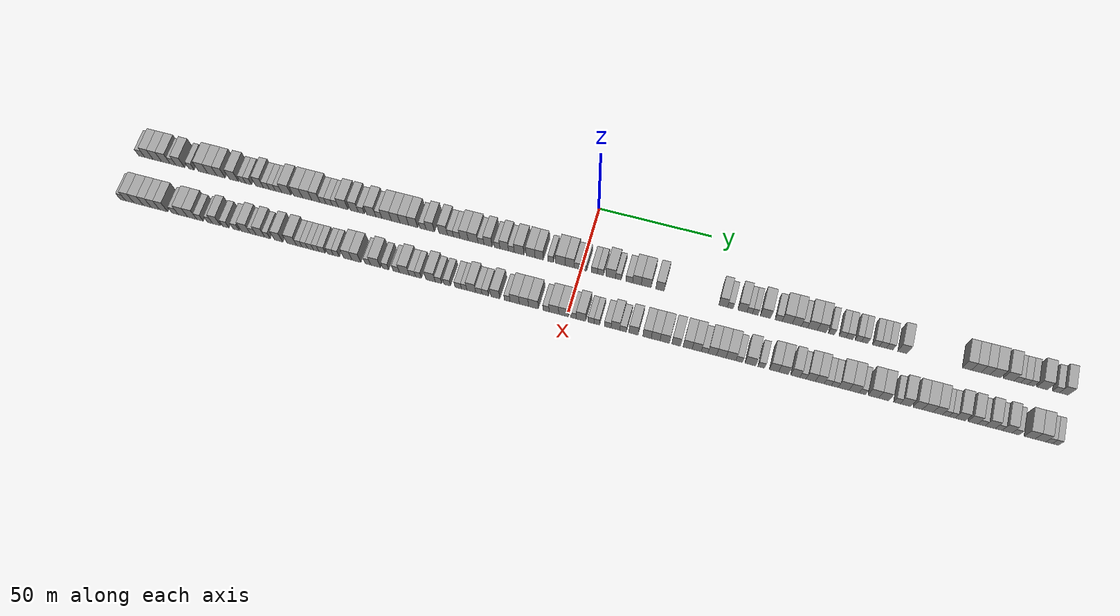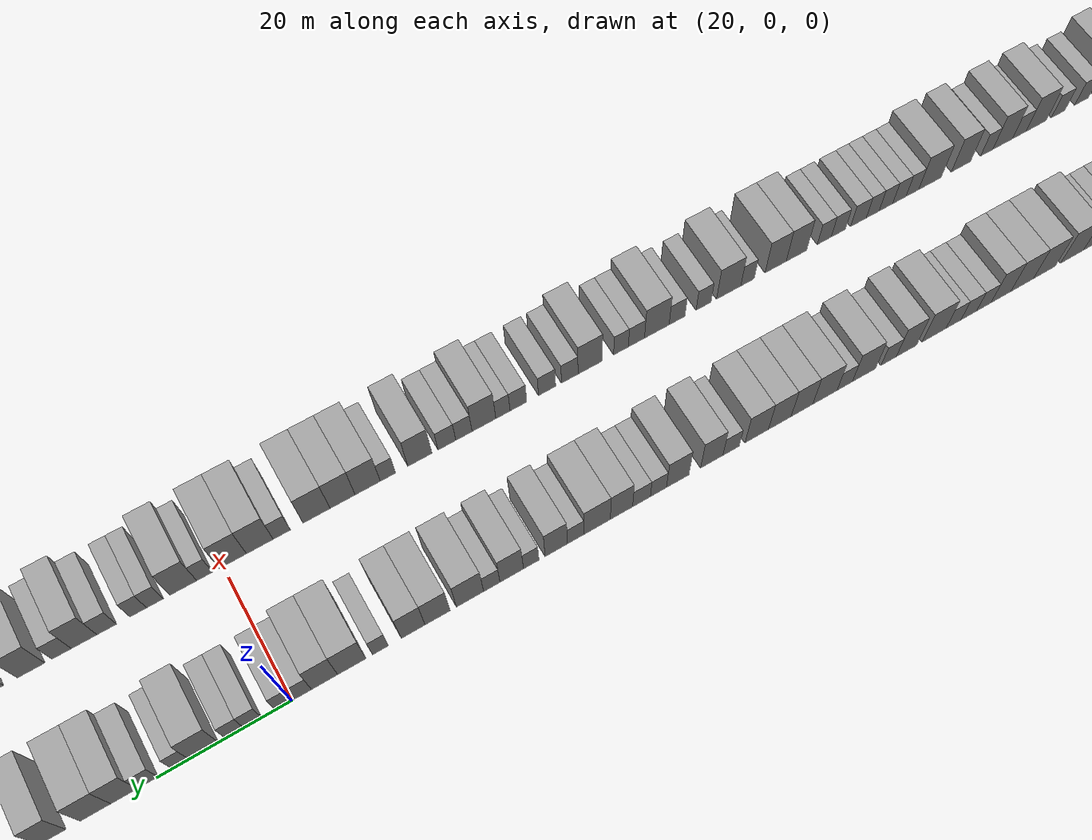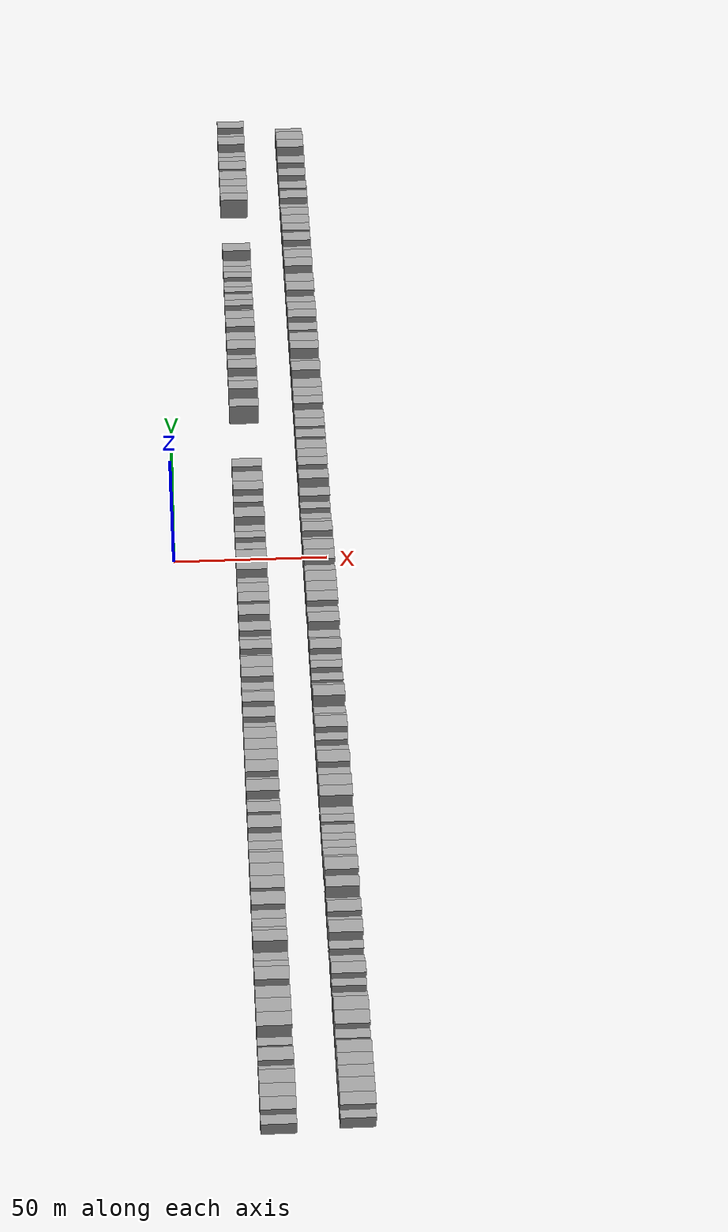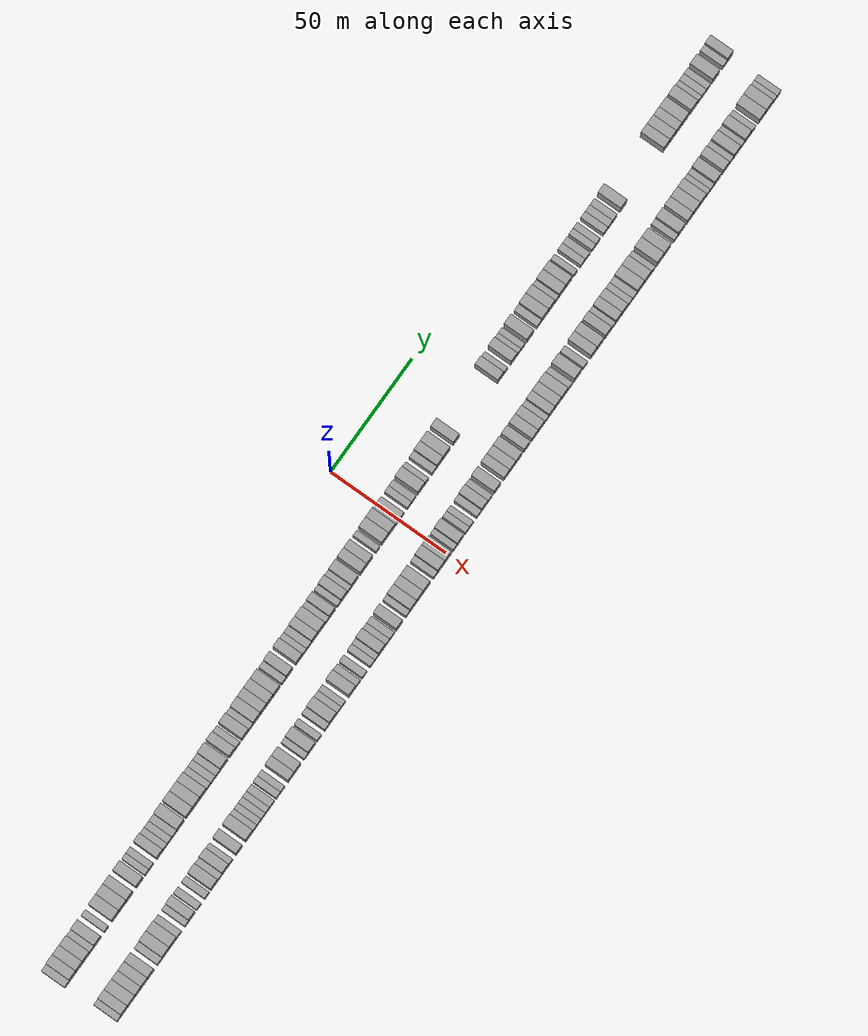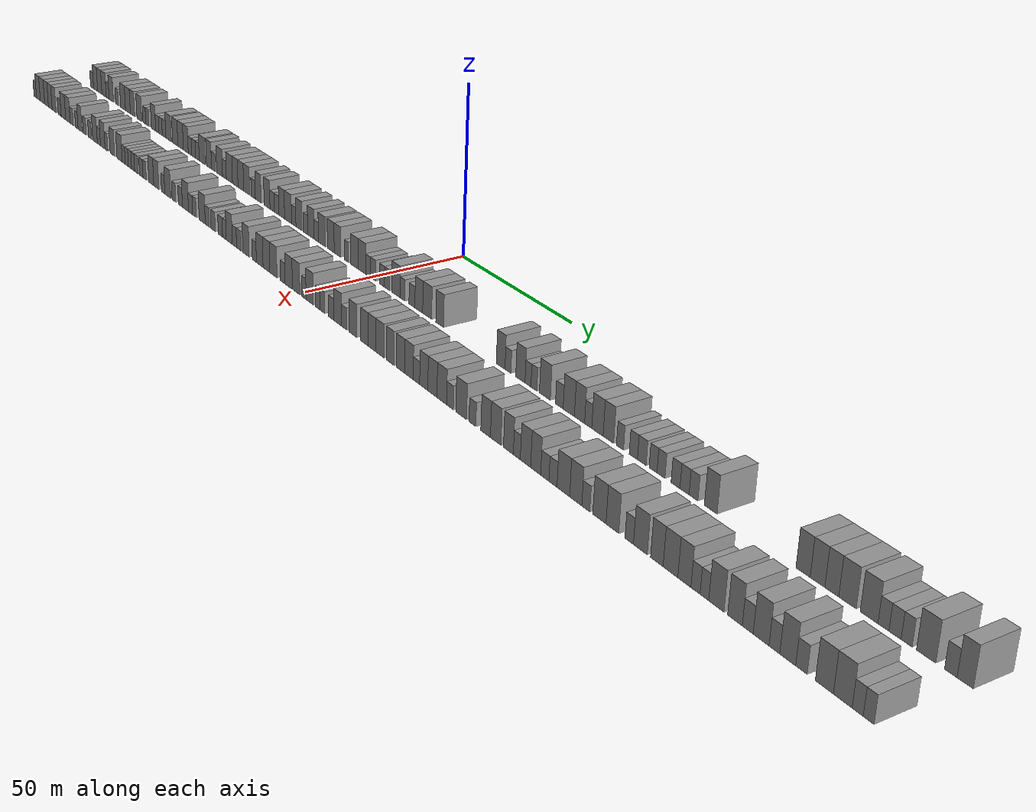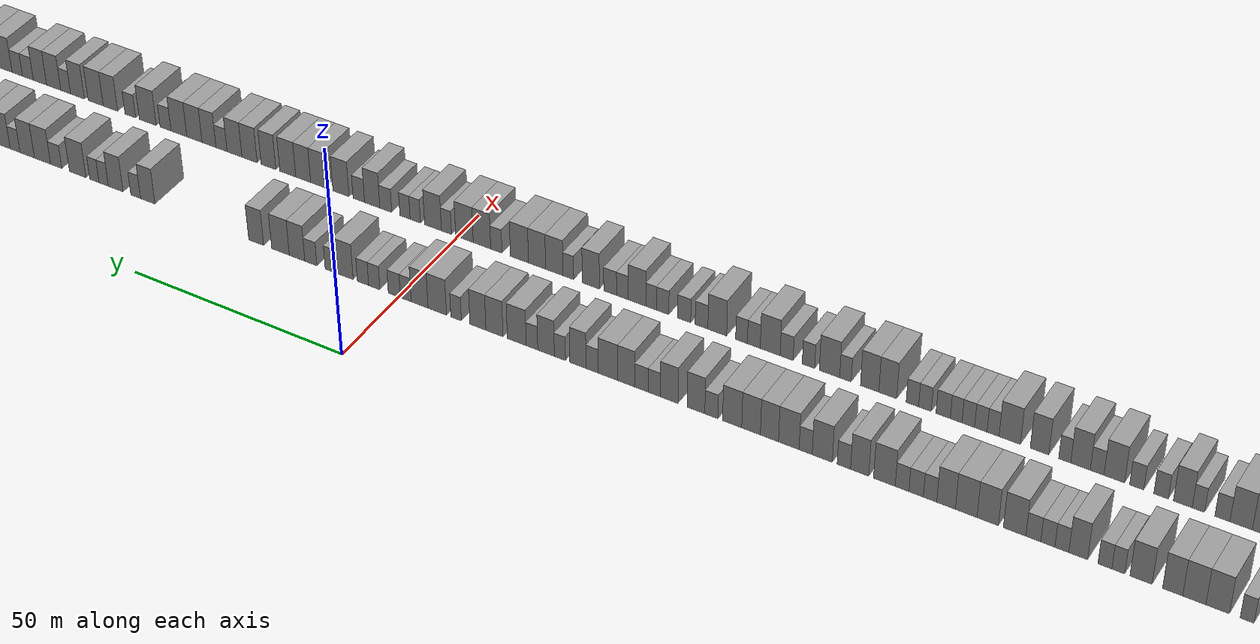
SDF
<sdf version="1.6">
 <world name="default">
  <scene>
   <sky><clouds><speed>12</speed></clouds></sky>
   <ambient>0.4 0.4 0.4 1</ambient>
   <background>0.7 0.7 0.7 1</background>
   <shadows>1</shadows>
  </scene>
  <gravity>0 0 -9.8066</gravity>
  <magnetic_field>6e-06 2.3e-05 -4.2e-05</magnetic_field>
  <physics default="0" name="default_physics" type="ode">
   <ode>
    <solver>
     <type>quick</type>
     <iters>10</iters>
     <sor>1.0</sor>
     <use_dynamic_moi_rescaling>0</use_dynamic_moi_rescaling>
    </solver>
    <constraints>
     <cfm>0</cfm>
     <erp>0.2</erp>
     <contact_max_correcting_vel>100</contact_max_correcting_vel>
     <contact_surface_layer>0.001</contact_surface_layer>
    </constraints>
   </ode>
   <max_step_size>0.004</max_step_size>
   <real_time_factor>1</real_time_factor>
   <real_time_update_rate>250</real_time_update_rate>
  </physics>
  <light name="sun" type="directional">
   <pose>0 0 10 0 0 0</pose>
   <diffuse>0.8 0.8 0.8 1</diffuse>
   <specular>0.2 0.2 0.2 1</specular>
   <attenuation>
    <range>1000</range>
    <constant>0.9</constant>
    <linear>0.01</linear>
    <quadratic>0.001</quadratic>
   </attenuation>
   <direction>-0.5 0.1 -0.9</direction>
  </light>
  <model name="building_1">
   <static>1</static>
   <pose>25.0000 -202.5261 0 0.000000 0.000000 0.000000</pose>
   <link name="link">
    <pose>0 0 3.00 0 0 0</pose>
    <collision name="collision"><geometry><box><size>10.0000 2.9478 6.0000</size></box></geometry></collision>
    <visual name="visual">
     <cast_shadows>0</cast_shadows>
     <geometry><box><size>10.0000 2.9478 6.0000</size></box></geometry>
     <material>
      <script>
       <uri>model://grey_wall/materials/scripts</uri>
       <uri>model://grey_wall/materials/textures</uri>
       <name>vrc/grey_wall</name>
      </script>
     </material>
    </visual>
   </link>
  </model>
  <model name="building_2">
   <static>1</static>
   <pose>25.0000 -199.0889 0 0.000000 0.000000 0.000000</pose>
   <link name="link">
    <pose>0 0 4.50 0 0 0</pose>
    <collision name="collision"><geometry><box><size>10.0000 3.9264 9.0000</size></box></geometry></collision>
    <visual name="visual">
     <cast_shadows>0</cast_shadows>
     <geometry><box><size>10.0000 3.9264 9.0000</size></box></geometry>
     <material>
      <script>
       <uri>model://grey_wall/materials/scripts</uri>
       <uri>model://grey_wall/materials/textures</uri>
       <name>vrc/grey_wall</name>
      </script>
     </material>
    </visual>
   </link>
  </model>
  <model name="building_3">
   <static>1</static>
   <pose>25.0000 -195.0800 0 0.000000 0.000000 0.000000</pose>
   <link name="link">
    <pose>0 0 4.50 0 0 0</pose>
    <collision name="collision"><geometry><box><size>10.0000 4.0915 9.0000</size></box></geometry></collision>
    <visual name="visual">
     <cast_shadows>0</cast_shadows>
     <geometry><box><size>10.0000 4.0915 9.0000</size></box></geometry>
     <material>
      <script>
       <uri>model://grey_wall/materials/scripts</uri>
       <uri>model://grey_wall/materials/textures</uri>
       <name>vrc/grey_wall</name>
      </script>
     </material>
    </visual>
   </link>
  </model>
  <model name="building_4">
   <static>1</static>
   <pose>25.0000 -190.9570 0 0.000000 0.000000 0.000000</pose>
   <link name="link">
    <pose>0 0 4.50 0 0 0</pose>
    <collision name="collision"><geometry><box><size>10.0000 4.1544 9.0000</size></box></geometry></collision>
    <visual name="visual">
     <cast_shadows>0</cast_shadows>
     <geometry><box><size>10.0000 4.1544 9.0000</size></box></geometry>
     <material>
      <script>
       <uri>model://grey_wall/materials/scripts</uri>
       <uri>model://grey_wall/materials/textures</uri>
       <name>vrc/grey_wall</name>
      </script>
     </material>
    </visual>
   </link>
  </model>
  <model name="building_5">
   <static>1</static>
   <pose>25.0000 -187.5378 0 0.000000 0.000000 0.000000</pose>
   <link name="link">
    <pose>0 0 3.00 0 0 0</pose>
    <collision name="collision"><geometry><box><size>10.0000 2.6841 6.0000</size></box></geometry></collision>
    <visual name="visual">
     <cast_shadows>0</cast_shadows>
     <geometry><box><size>10.0000 2.6841 6.0000</size></box></geometry>
     <material>
      <script>
       <uri>model://grey_wall/materials/scripts</uri>
       <uri>model://grey_wall/materials/textures</uri>
       <name>vrc/grey_wall</name>
      </script>
     </material>
    </visual>
   </link>
  </model>
  <model name="building_6">
   <static>1</static>
   <pose>25.0000 -184.1339 0 0.000000 0.000000 0.000000</pose>
   <link name="link">
    <pose>0 0 4.50 0 0 0</pose>
    <collision name="collision"><geometry><box><size>10.0000 4.1236 9.0000</size></box></geometry></collision>
    <visual name="visual">
     <cast_shadows>0</cast_shadows>
     <geometry><box><size>10.0000 4.1236 9.0000</size></box></geometry>
     <material>
      <script>
       <uri>model://grey_wall/materials/scripts</uri>
       <uri>model://grey_wall/materials/textures</uri>
       <name>vrc/grey_wall</name>
      </script>
     </material>
    </visual>
   </link>
  </model>
  <model name="building_7">
   <static>1</static>
   <pose>25.0000 -178.7740 0 0.000000 0.000000 0.000000</pose>
   <link name="link">
    <pose>0 0 3.00 0 0 0</pose>
    <collision name="collision"><geometry><box><size>10.0000 2.5963 6.0000</size></box></geometry></collision>
    <visual name="visual">
     <cast_shadows>0</cast_shadows>
     <geometry><box><size>10.0000 2.5963 6.0000</size></box></geometry>
     <material>
      <script>
       <uri>model://grey_wall/materials/scripts</uri>
       <uri>model://grey_wall/materials/textures</uri>
       <name>vrc/grey_wall</name>
      </script>
     </material>
    </visual>
   </link>
  </model>
  <model name="building_8">
   <static>1</static>
   <pose>25.0000 -173.2522 0 0.000000 0.000000 0.000000</pose>
   <link name="link">
    <pose>0 0 4.50 0 0 0</pose>
    <collision name="collision"><geometry><box><size>10.0000 4.4474 9.0000</size></box></geometry></collision>
    <visual name="visual">
     <cast_shadows>0</cast_shadows>
     <geometry><box><size>10.0000 4.4474 9.0000</size></box></geometry>
     <material>
      <script>
       <uri>model://grey_wall/materials/scripts</uri>
       <uri>model://grey_wall/materials/textures</uri>
       <name>vrc/grey_wall</name>
      </script>
     </material>
    </visual>
   </link>
  </model>
  <model name="building_9">
   <static>1</static>
   <pose>25.0000 -168.8298 0 0.000000 0.000000 0.000000</pose>
   <link name="link">
    <pose>0 0 4.50 0 0 0</pose>
    <collision name="collision"><geometry><box><size>10.0000 4.3973 9.0000</size></box></geometry></collision>
    <visual name="visual">
     <cast_shadows>0</cast_shadows>
     <geometry><box><size>10.0000 4.3973 9.0000</size></box></geometry>
     <material>
      <script>
       <uri>model://grey_wall/materials/scripts</uri>
       <uri>model://grey_wall/materials/textures</uri>
       <name>vrc/grey_wall</name>
      </script>
     </material>
    </visual>
   </link>
  </model>
  <model name="building_10">
   <static>1</static>
   <pose>25.0000 -164.7153 0 0.000000 0.000000 0.000000</pose>
   <link name="link">
    <pose>0 0 4.50 0 0 0</pose>
    <collision name="collision"><geometry><box><size>10.0000 3.8318 9.0000</size></box></geometry></collision>
    <visual name="visual">
     <cast_shadows>0</cast_shadows>
     <geometry><box><size>10.0000 3.8318 9.0000</size></box></geometry>
     <material>
      <script>
       <uri>model://grey_wall/materials/scripts</uri>
       <uri>model://grey_wall/materials/textures</uri>
       <name>vrc/grey_wall</name>
      </script>
     </material>
    </visual>
   </link>
  </model>
  <model name="building_11">
   <static>1</static>
   <pose>25.0000 -158.6673 0 0.000000 0.000000 0.000000</pose>
   <link name="link">
    <pose>0 0 4.50 0 0 0</pose>
    <collision name="collision"><geometry><box><size>10.0000 4.2642 9.0000</size></box></geometry></collision>
    <visual name="visual">
     <cast_shadows>0</cast_shadows>
     <geometry><box><size>10.0000 4.2642 9.0000</size></box></geometry>
     <material>
      <script>
       <uri>model://grey_wall/materials/scripts</uri>
       <uri>model://grey_wall/materials/textures</uri>
       <name>vrc/grey_wall</name>
      </script>
     </material>
    </visual>
   </link>
  </model>
  <model name="building_12">
   <static>1</static>
   <pose>25.0000 -154.2892 0 0.000000 0.000000 0.000000</pose>
   <link name="link">
    <pose>0 0 3.00 0 0 0</pose>
    <collision name="collision"><geometry><box><size>10.0000 2.4920 6.0000</size></box></geometry></collision>
    <visual name="visual">
     <cast_shadows>0</cast_shadows>
     <geometry><box><size>10.0000 2.4920 6.0000</size></box></geometry>
     <material>
      <script>
       <uri>model://grey_wall/materials/scripts</uri>
       <uri>model://grey_wall/materials/textures</uri>
       <name>vrc/grey_wall</name>
      </script>
     </material>
    </visual>
   </link>
  </model>
  <model name="building_13">
   <static>1</static>
   <pose>25.0000 -151.6903 0 0.000000 0.000000 0.000000</pose>
   <link name="link">
    <pose>0 0 3.00 0 0 0</pose>
    <collision name="collision"><geometry><box><size>10.0000 2.7059 6.0000</size></box></geometry></collision>
    <visual name="visual">
     <cast_shadows>0</cast_shadows>
     <geometry><box><size>10.0000 2.7059 6.0000</size></box></geometry>
     <material>
      <script>
       <uri>model://grey_wall/materials/scripts</uri>
       <uri>model://grey_wall/materials/textures</uri>
       <name>vrc/grey_wall</name>
      </script>
     </material>
    </visual>
   </link>
  </model>
  <model name="building_14">
   <static>1</static>
   <pose>25.0000 -146.4922 0 0.000000 0.000000 0.000000</pose>
   <link name="link">
    <pose>0 0 4.50 0 0 0</pose>
    <collision name="collision"><geometry><box><size>10.0000 3.6902 9.0000</size></box></geometry></collision>
    <visual name="visual">
     <cast_shadows>0</cast_shadows>
     <geometry><box><size>10.0000 3.6902 9.0000</size></box></geometry>
     <material>
      <script>
       <uri>model://grey_wall/materials/scripts</uri>
       <uri>model://grey_wall/materials/textures</uri>
       <name>vrc/grey_wall</name>
      </script>
     </material>
    </visual>
   </link>
  </model>
  <model name="building_15">
   <static>1</static>
   <pose>25.0000 -143.2801 0 0.000000 0.000000 0.000000</pose>
   <link name="link">
    <pose>0 0 3.00 0 0 0</pose>
    <collision name="collision"><geometry><box><size>10.0000 2.7340 6.0000</size></box></geometry></collision>
    <visual name="visual">
     <cast_shadows>0</cast_shadows>
     <geometry><box><size>10.0000 2.7340 6.0000</size></box></geometry>
     <material>
      <script>
       <uri>model://grey_wall/materials/scripts</uri>
       <uri>model://grey_wall/materials/textures</uri>
       <name>vrc/grey_wall</name>
      </script>
     </material>
    </visual>
   </link>
  </model>
  <model name="building_16">
   <static>1</static>
   <pose>25.0000 -140.5237 0 0.000000 0.000000 0.000000</pose>
   <link name="link">
    <pose>0 0 3.00 0 0 0</pose>
    <collision name="collision"><geometry><box><size>10.0000 2.7788 6.0000</size></box></geometry></collision>
    <visual name="visual">
     <cast_shadows>0</cast_shadows>
     <geometry><box><size>10.0000 2.7788 6.0000</size></box></geometry>
     <material>
      <script>
       <uri>model://grey_wall/materials/scripts</uri>
       <uri>model://grey_wall/materials/textures</uri>
       <name>vrc/grey_wall</name>
      </script>
     </material>
    </visual>
   </link>
  </model>
  <model name="building_17">
   <static>1</static>
   <pose>25.0000 -137.6611 0 0.000000 0.000000 0.000000</pose>
   <link name="link">
    <pose>0 0 3.00 0 0 0</pose>
    <collision name="collision"><geometry><box><size>10.0000 2.9464 6.0000</size></box></geometry></collision>
    <visual name="visual">
     <cast_shadows>0</cast_shadows>
     <geometry><box><size>10.0000 2.9464 6.0000</size></box></geometry>
     <material>
      <script>
       <uri>model://grey_wall/materials/scripts</uri>
       <uri>model://grey_wall/materials/textures</uri>
       <name>vrc/grey_wall</name>
      </script>
     </material>
    </visual>
   </link>
  </model>
  <model name="building_18">
   <static>1</static>
   <pose>25.0000 -133.9481 0 0.000000 0.000000 0.000000</pose>
   <link name="link">
    <pose>0 0 4.50 0 0 0</pose>
    <collision name="collision"><geometry><box><size>10.0000 4.4797 9.0000</size></box></geometry></collision>
    <visual name="visual">
     <cast_shadows>0</cast_shadows>
     <geometry><box><size>10.0000 4.4797 9.0000</size></box></geometry>
     <material>
      <script>
       <uri>model://grey_wall/materials/scripts</uri>
       <uri>model://grey_wall/materials/textures</uri>
       <name>vrc/grey_wall</name>
      </script>
     </material>
    </visual>
   </link>
  </model>
  <model name="building_19">
   <static>1</static>
   <pose>25.0000 -128.5693 0 0.000000 0.000000 0.000000</pose>
   <link name="link">
    <pose>0 0 4.50 0 0 0</pose>
    <collision name="collision"><geometry><box><size>10.0000 4.2778 9.0000</size></box></geometry></collision>
    <visual name="visual">
     <cast_shadows>0</cast_shadows>
     <geometry><box><size>10.0000 4.2778 9.0000</size></box></geometry>
     <material>
      <script>
       <uri>model://grey_wall/materials/scripts</uri>
       <uri>model://grey_wall/materials/textures</uri>
       <name>vrc/grey_wall</name>
      </script>
     </material>
    </visual>
   </link>
  </model>
  <model name="building_20">
   <static>1</static>
   <pose>25.0000 -124.2486 0 0.000000 0.000000 0.000000</pose>
   <link name="link">
    <pose>0 0 4.50 0 0 0</pose>
    <collision name="collision"><geometry><box><size>10.0000 4.3637 9.0000</size></box></geometry></collision>
    <visual name="visual">
     <cast_shadows>0</cast_shadows>
     <geometry><box><size>10.0000 4.3637 9.0000</size></box></geometry>
     <material>
      <script>
       <uri>model://grey_wall/materials/scripts</uri>
       <uri>model://grey_wall/materials/textures</uri>
       <name>vrc/grey_wall</name>
      </script>
     </material>
    </visual>
   </link>
  </model>
  <model name="building_21">
   <static>1</static>
   <pose>25.0000 -120.1668 0 0.000000 0.000000 0.000000</pose>
   <link name="link">
    <pose>0 0 4.50 0 0 0</pose>
    <collision name="collision"><geometry><box><size>10.0000 3.8000 9.0000</size></box></geometry></collision>
    <visual name="visual">
     <cast_shadows>0</cast_shadows>
     <geometry><box><size>10.0000 3.8000 9.0000</size></box></geometry>
     <material>
      <script>
       <uri>model://grey_wall/materials/scripts</uri>
       <uri>model://grey_wall/materials/textures</uri>
       <name>vrc/grey_wall</name>
      </script>
     </material>
    </visual>
   </link>
  </model>
  <model name="building_22">
   <static>1</static>
   <pose>25.0000 -116.9023 0 0.000000 0.000000 0.000000</pose>
   <link name="link">
    <pose>0 0 3.00 0 0 0</pose>
    <collision name="collision"><geometry><box><size>10.0000 2.7288 6.0000</size></box></geometry></collision>
    <visual name="visual">
     <cast_shadows>0</cast_shadows>
     <geometry><box><size>10.0000 2.7288 6.0000</size></box></geometry>
     <material>
      <script>
       <uri>model://grey_wall/materials/scripts</uri>
       <uri>model://grey_wall/materials/textures</uri>
       <name>vrc/grey_wall</name>
      </script>
     </material>
    </visual>
   </link>
  </model>
  <model name="building_23">
   <static>1</static>
   <pose>25.0000 -114.0692 0 0.000000 0.000000 0.000000</pose>
   <link name="link">
    <pose>0 0 3.00 0 0 0</pose>
    <collision name="collision"><geometry><box><size>10.0000 2.9374 6.0000</size></box></geometry></collision>
    <visual name="visual">
     <cast_shadows>0</cast_shadows>
     <geometry><box><size>10.0000 2.9374 6.0000</size></box></geometry>
     <material>
      <script>
       <uri>model://grey_wall/materials/scripts</uri>
       <uri>model://grey_wall/materials/textures</uri>
       <name>vrc/grey_wall</name>
      </script>
     </material>
    </visual>
   </link>
  </model>
  <model name="building_24">
   <static>1</static>
   <pose>25.0000 -111.1918 0 0.000000 0.000000 0.000000</pose>
   <link name="link">
    <pose>0 0 3.00 0 0 0</pose>
    <collision name="collision"><geometry><box><size>10.0000 2.8174 6.0000</size></box></geometry></collision>
    <visual name="visual">
     <cast_shadows>0</cast_shadows>
     <geometry><box><size>10.0000 2.8174 6.0000</size></box></geometry>
     <material>
      <script>
       <uri>model://grey_wall/materials/scripts</uri>
       <uri>model://grey_wall/materials/textures</uri>
       <name>vrc/grey_wall</name>
      </script>
     </material>
    </visual>
   </link>
  </model>
  <model name="building_25">
   <static>1</static>
   <pose>25.0000 -107.5457 0 0.000000 0.000000 0.000000</pose>
   <link name="link">
    <pose>0 0 4.50 0 0 0</pose>
    <collision name="collision"><geometry><box><size>10.0000 4.4749 9.0000</size></box></geometry></collision>
    <visual name="visual">
     <cast_shadows>0</cast_shadows>
     <geometry><box><size>10.0000 4.4749 9.0000</size></box></geometry>
     <material>
      <script>
       <uri>model://grey_wall/materials/scripts</uri>
       <uri>model://grey_wall/materials/textures</uri>
       <name>vrc/grey_wall</name>
      </script>
     </material>
    </visual>
   </link>
  </model>
  <model name="building_26">
   <static>1</static>
   <pose>25.0000 -102.4200 0 0.000000 0.000000 0.000000</pose>
   <link name="link">
    <pose>0 0 4.50 0 0 0</pose>
    <collision name="collision"><geometry><box><size>10.0000 3.7764 9.0000</size></box></geometry></collision>
    <visual name="visual">
     <cast_shadows>0</cast_shadows>
     <geometry><box><size>10.0000 3.7764 9.0000</size></box></geometry>
     <material>
      <script>
       <uri>model://grey_wall/materials/scripts</uri>
       <uri>model://grey_wall/materials/textures</uri>
       <name>vrc/grey_wall</name>
      </script>
     </material>
    </visual>
   </link>
  </model>
  <model name="building_27">
   <static>1</static>
   <pose>25.0000 -99.1316 0 0.000000 0.000000 0.000000</pose>
   <link name="link">
    <pose>0 0 3.00 0 0 0</pose>
    <collision name="collision"><geometry><box><size>10.0000 2.8005 6.0000</size></box></geometry></collision>
    <visual name="visual">
     <cast_shadows>0</cast_shadows>
     <geometry><box><size>10.0000 2.8005 6.0000</size></box></geometry>
     <material>
      <script>
       <uri>model://grey_wall/materials/scripts</uri>
       <uri>model://grey_wall/materials/textures</uri>
       <name>vrc/grey_wall</name>
      </script>
     </material>
    </visual>
   </link>
  </model>
  <model name="building_28">
   <static>1</static>
   <pose>25.0000 -94.6144 0 0.000000 0.000000 0.000000</pose>
   <link name="link">
    <pose>0 0 4.50 0 0 0</pose>
    <collision name="collision"><geometry><box><size>10.0000 4.2339 9.0000</size></box></geometry></collision>
    <visual name="visual">
     <cast_shadows>0</cast_shadows>
     <geometry><box><size>10.0000 4.2339 9.0000</size></box></geometry>
     <material>
      <script>
       <uri>model://grey_wall/materials/scripts</uri>
       <uri>model://grey_wall/materials/textures</uri>
       <name>vrc/grey_wall</name>
      </script>
     </material>
    </visual>
   </link>
  </model>
  <model name="building_29">
   <static>1</static>
   <pose>25.0000 -91.1140 0 0.000000 0.000000 0.000000</pose>
   <link name="link">
    <pose>0 0 3.00 0 0 0</pose>
    <collision name="collision"><geometry><box><size>10.0000 2.7668 6.0000</size></box></geometry></collision>
    <visual name="visual">
     <cast_shadows>0</cast_shadows>
     <geometry><box><size>10.0000 2.7668 6.0000</size></box></geometry>
     <material>
      <script>
       <uri>model://grey_wall/materials/scripts</uri>
       <uri>model://grey_wall/materials/textures</uri>
       <name>vrc/grey_wall</name>
      </script>
     </material>
    </visual>
   </link>
  </model>
  <model name="building_30">
   <static>1</static>
   <pose>25.0000 -87.5491 0 0.000000 0.000000 0.000000</pose>
   <link name="link">
    <pose>0 0 4.50 0 0 0</pose>
    <collision name="collision"><geometry><box><size>10.0000 4.3629 9.0000</size></box></geometry></collision>
    <visual name="visual">
     <cast_shadows>0</cast_shadows>
     <geometry><box><size>10.0000 4.3629 9.0000</size></box></geometry>
     <material>
      <script>
       <uri>model://grey_wall/materials/scripts</uri>
       <uri>model://grey_wall/materials/textures</uri>
       <name>vrc/grey_wall</name>
      </script>
     </material>
    </visual>
   </link>
  </model>
  <model name="building_31">
   <static>1</static>
   <pose>25.0000 -83.4350 0 0.000000 0.000000 0.000000</pose>
   <link name="link">
    <pose>0 0 4.50 0 0 0</pose>
    <collision name="collision"><geometry><box><size>10.0000 3.8654 9.0000</size></box></geometry></collision>
    <visual name="visual">
     <cast_shadows>0</cast_shadows>
     <geometry><box><size>10.0000 3.8654 9.0000</size></box></geometry>
     <material>
      <script>
       <uri>model://grey_wall/materials/scripts</uri>
       <uri>model://grey_wall/materials/textures</uri>
       <name>vrc/grey_wall</name>
      </script>
     </material>
    </visual>
   </link>
  </model>
  <model name="building_32">
   <static>1</static>
   <pose>25.0000 -79.5037 0 0.000000 0.000000 0.000000</pose>
   <link name="link">
    <pose>0 0 4.50 0 0 0</pose>
    <collision name="collision"><geometry><box><size>10.0000 3.9973 9.0000</size></box></geometry></collision>
    <visual name="visual">
     <cast_shadows>0</cast_shadows>
     <geometry><box><size>10.0000 3.9973 9.0000</size></box></geometry>
     <material>
      <script>
       <uri>model://grey_wall/materials/scripts</uri>
       <uri>model://grey_wall/materials/textures</uri>
       <name>vrc/grey_wall</name>
      </script>
     </material>
    </visual>
   </link>
  </model>
  <model name="building_33">
   <static>1</static>
   <pose>25.0000 -75.4474 0 0.000000 0.000000 0.000000</pose>
   <link name="link">
    <pose>0 0 4.50 0 0 0</pose>
    <collision name="collision"><geometry><box><size>10.0000 4.1154 9.0000</size></box></geometry></collision>
    <visual name="visual">
     <cast_shadows>0</cast_shadows>
     <geometry><box><size>10.0000 4.1154 9.0000</size></box></geometry>
     <material>
      <script>
       <uri>model://grey_wall/materials/scripts</uri>
       <uri>model://grey_wall/materials/textures</uri>
       <name>vrc/grey_wall</name>
      </script>
     </material>
    </visual>
   </link>
  </model>
  <model name="building_34">
   <static>1</static>
   <pose>25.0000 -70.9645 0 0.000000 0.000000 0.000000</pose>
   <link name="link">
    <pose>0 0 3.00 0 0 0</pose>
    <collision name="collision"><geometry><box><size>10.0000 2.8503 6.0000</size></box></geometry></collision>
    <visual name="visual">
     <cast_shadows>0</cast_shadows>
     <geometry><box><size>10.0000 2.8503 6.0000</size></box></geometry>
     <material>
      <script>
       <uri>model://grey_wall/materials/scripts</uri>
       <uri>model://grey_wall/materials/textures</uri>
       <name>vrc/grey_wall</name>
      </script>
     </material>
    </visual>
   </link>
  </model>
  <model name="building_35">
   <static>1</static>
   <pose>25.0000 -67.6166 0 0.000000 0.000000 0.000000</pose>
   <link name="link">
    <pose>0 0 4.50 0 0 0</pose>
    <collision name="collision"><geometry><box><size>10.0000 3.8455 9.0000</size></box></geometry></collision>
    <visual name="visual">
     <cast_shadows>0</cast_shadows>
     <geometry><box><size>10.0000 3.8455 9.0000</size></box></geometry>
     <material>
      <script>
       <uri>model://grey_wall/materials/scripts</uri>
       <uri>model://grey_wall/materials/textures</uri>
       <name>vrc/grey_wall</name>
      </script>
     </material>
    </visual>
   </link>
  </model>
  <model name="building_36">
   <static>1</static>
   <pose>25.0000 -61.7630 0 0.000000 0.000000 0.000000</pose>
   <link name="link">
    <pose>0 0 4.50 0 0 0</pose>
    <collision name="collision"><geometry><box><size>10.0000 3.8618 9.0000</size></box></geometry></collision>
    <visual name="visual">
     <cast_shadows>0</cast_shadows>
     <geometry><box><size>10.0000 3.8618 9.0000</size></box></geometry>
     <material>
      <script>
       <uri>model://grey_wall/materials/scripts</uri>
       <uri>model://grey_wall/materials/textures</uri>
       <name>vrc/grey_wall</name>
      </script>
     </material>
    </visual>
   </link>
  </model>
  <model name="building_37">
   <static>1</static>
   <pose>25.0000 -58.4791 0 0.000000 0.000000 0.000000</pose>
   <link name="link">
    <pose>0 0 3.00 0 0 0</pose>
    <collision name="collision"><geometry><box><size>10.0000 2.7060 6.0000</size></box></geometry></collision>
    <visual name="visual">
     <cast_shadows>0</cast_shadows>
     <geometry><box><size>10.0000 2.7060 6.0000</size></box></geometry>
     <material>
      <script>
       <uri>model://grey_wall/materials/scripts</uri>
       <uri>model://grey_wall/materials/textures</uri>
       <name>vrc/grey_wall</name>
      </script>
     </material>
    </visual>
   </link>
  </model>
  <model name="building_38">
   <static>1</static>
   <pose>25.0000 -55.6310 0 0.000000 0.000000 0.000000</pose>
   <link name="link">
    <pose>0 0 3.00 0 0 0</pose>
    <collision name="collision"><geometry><box><size>10.0000 2.9903 6.0000</size></box></geometry></collision>
    <visual name="visual">
     <cast_shadows>0</cast_shadows>
     <geometry><box><size>10.0000 2.9903 6.0000</size></box></geometry>
     <material>
      <script>
       <uri>model://grey_wall/materials/scripts</uri>
       <uri>model://grey_wall/materials/textures</uri>
       <name>vrc/grey_wall</name>
      </script>
     </material>
    </visual>
   </link>
  </model>
  <model name="building_39">
   <static>1</static>
   <pose>25.0000 -52.2686 0 0.000000 0.000000 0.000000</pose>
   <link name="link">
    <pose>0 0 4.50 0 0 0</pose>
    <collision name="collision"><geometry><box><size>10.0000 3.7345 9.0000</size></box></geometry></collision>
    <visual name="visual">
     <cast_shadows>0</cast_shadows>
     <geometry><box><size>10.0000 3.7345 9.0000</size></box></geometry>
     <material>
      <script>
       <uri>model://grey_wall/materials/scripts</uri>
       <uri>model://grey_wall/materials/textures</uri>
       <name>vrc/grey_wall</name>
      </script>
     </material>
    </visual>
   </link>
  </model>
  <model name="building_40">
   <static>1</static>
   <pose>25.0000 -48.2032 0 0.000000 0.000000 0.000000</pose>
   <link name="link">
    <pose>0 0 4.50 0 0 0</pose>
    <collision name="collision"><geometry><box><size>10.0000 4.3964 9.0000</size></box></geometry></collision>
    <visual name="visual">
     <cast_shadows>0</cast_shadows>
     <geometry><box><size>10.0000 4.3964 9.0000</size></box></geometry>
     <material>
      <script>
       <uri>model://grey_wall/materials/scripts</uri>
       <uri>model://grey_wall/materials/textures</uri>
       <name>vrc/grey_wall</name>
      </script>
     </material>
    </visual>
   </link>
  </model>
  <model name="building_41">
   <static>1</static>
   <pose>25.0000 -44.6476 0 0.000000 0.000000 0.000000</pose>
   <link name="link">
    <pose>0 0 3.00 0 0 0</pose>
    <collision name="collision"><geometry><box><size>10.0000 2.7148 6.0000</size></box></geometry></collision>
    <visual name="visual">
     <cast_shadows>0</cast_shadows>
     <geometry><box><size>10.0000 2.7148 6.0000</size></box></geometry>
     <material>
      <script>
       <uri>model://grey_wall/materials/scripts</uri>
       <uri>model://grey_wall/materials/textures</uri>
       <name>vrc/grey_wall</name>
      </script>
     </material>
    </visual>
   </link>
  </model>
  <model name="building_42">
   <static>1</static>
   <pose>25.0000 -41.4667 0 0.000000 0.000000 0.000000</pose>
   <link name="link">
    <pose>0 0 4.50 0 0 0</pose>
    <collision name="collision"><geometry><box><size>10.0000 3.6469 9.0000</size></box></geometry></collision>
    <visual name="visual">
     <cast_shadows>0</cast_shadows>
     <geometry><box><size>10.0000 3.6469 9.0000</size></box></geometry>
     <material>
      <script>
       <uri>model://grey_wall/materials/scripts</uri>
       <uri>model://grey_wall/materials/textures</uri>
       <name>vrc/grey_wall</name>
      </script>
     </material>
    </visual>
   </link>
  </model>
  <model name="building_43">
   <static>1</static>
   <pose>25.0000 -37.3886 0 0.000000 0.000000 0.000000</pose>
   <link name="link">
    <pose>0 0 3.00 0 0 0</pose>
    <collision name="collision"><geometry><box><size>10.0000 2.5093 6.0000</size></box></geometry></collision>
    <visual name="visual">
     <cast_shadows>0</cast_shadows>
     <geometry><box><size>10.0000 2.5093 6.0000</size></box></geometry>
     <material>
      <script>
       <uri>model://grey_wall/materials/scripts</uri>
       <uri>model://grey_wall/materials/textures</uri>
       <name>vrc/grey_wall</name>
      </script>
     </material>
    </visual>
   </link>
  </model>
  <model name="building_44">
   <static>1</static>
   <pose>25.0000 -34.2427 0 0.000000 0.000000 0.000000</pose>
   <link name="link">
    <pose>0 0 4.50 0 0 0</pose>
    <collision name="collision"><geometry><box><size>10.0000 3.7825 9.0000</size></box></geometry></collision>
    <visual name="visual">
     <cast_shadows>0</cast_shadows>
     <geometry><box><size>10.0000 3.7825 9.0000</size></box></geometry>
     <material>
      <script>
       <uri>model://grey_wall/materials/scripts</uri>
       <uri>model://grey_wall/materials/textures</uri>
       <name>vrc/grey_wall</name>
      </script>
     </material>
    </visual>
   </link>
  </model>
  <model name="building_45">
   <static>1</static>
   <pose>25.0000 -31.0395 0 0.000000 0.000000 0.000000</pose>
   <link name="link">
    <pose>0 0 3.00 0 0 0</pose>
    <collision name="collision"><geometry><box><size>10.0000 2.6238 6.0000</size></box></geometry></collision>
    <visual name="visual">
     <cast_shadows>0</cast_shadows>
     <geometry><box><size>10.0000 2.6238 6.0000</size></box></geometry>
     <material>
      <script>
       <uri>model://grey_wall/materials/scripts</uri>
       <uri>model://grey_wall/materials/textures</uri>
       <name>vrc/grey_wall</name>
      </script>
     </material>
    </visual>
   </link>
  </model>
  <model name="building_46">
   <static>1</static>
   <pose>25.0000 -27.5578 0 0.000000 0.000000 0.000000</pose>
   <link name="link">
    <pose>0 0 4.50 0 0 0</pose>
    <collision name="collision"><geometry><box><size>10.0000 4.3396 9.0000</size></box></geometry></collision>
    <visual name="visual">
     <cast_shadows>0</cast_shadows>
     <geometry><box><size>10.0000 4.3396 9.0000</size></box></geometry>
     <material>
      <script>
       <uri>model://grey_wall/materials/scripts</uri>
       <uri>model://grey_wall/materials/textures</uri>
       <name>vrc/grey_wall</name>
      </script>
     </material>
    </visual>
   </link>
  </model>
  <model name="building_47">
   <static>1</static>
   <pose>25.0000 -22.4125 0 0.000000 0.000000 0.000000</pose>
   <link name="link">
    <pose>0 0 4.50 0 0 0</pose>
    <collision name="collision"><geometry><box><size>10.0000 3.9510 9.0000</size></box></geometry></collision>
    <visual name="visual">
     <cast_shadows>0</cast_shadows>
     <geometry><box><size>10.0000 3.9510 9.0000</size></box></geometry>
     <material>
      <script>
       <uri>model://grey_wall/materials/scripts</uri>
       <uri>model://grey_wall/materials/textures</uri>
       <name>vrc/grey_wall</name>
      </script>
     </material>
    </visual>
   </link>
  </model>
  <model name="building_48">
   <static>1</static>
   <pose>25.0000 -18.5852 0 0.000000 0.000000 0.000000</pose>
   <link name="link">
    <pose>0 0 4.50 0 0 0</pose>
    <collision name="collision"><geometry><box><size>10.0000 3.7035 9.0000</size></box></geometry></collision>
    <visual name="visual">
     <cast_shadows>0</cast_shadows>
     <geometry><box><size>10.0000 3.7035 9.0000</size></box></geometry>
     <material>
      <script>
       <uri>model://grey_wall/materials/scripts</uri>
       <uri>model://grey_wall/materials/textures</uri>
       <name>vrc/grey_wall</name>
      </script>
     </material>
    </visual>
   </link>
  </model>
  <model name="building_49">
   <static>1</static>
   <pose>25.0000 -13.5009 0 0.000000 0.000000 0.000000</pose>
   <link name="link">
    <pose>0 0 3.00 0 0 0</pose>
    <collision name="collision"><geometry><box><size>10.0000 2.4650 6.0000</size></box></geometry></collision>
    <visual name="visual">
     <cast_shadows>0</cast_shadows>
     <geometry><box><size>10.0000 2.4650 6.0000</size></box></geometry>
     <material>
      <script>
       <uri>model://grey_wall/materials/scripts</uri>
       <uri>model://grey_wall/materials/textures</uri>
       <name>vrc/grey_wall</name>
      </script>
     </material>
    </visual>
   </link>
  </model>
  <model name="building_50">
   <static>1</static>
   <pose>25.0000 -9.0955 0 0.000000 0.000000 0.000000</pose>
   <link name="link">
    <pose>0 0 4.50 0 0 0</pose>
    <collision name="collision"><geometry><box><size>10.0000 4.3460 9.0000</size></box></geometry></collision>
    <visual name="visual">
     <cast_shadows>0</cast_shadows>
     <geometry><box><size>10.0000 4.3460 9.0000</size></box></geometry>
     <material>
      <script>
       <uri>model://grey_wall/materials/scripts</uri>
       <uri>model://grey_wall/materials/textures</uri>
       <name>vrc/grey_wall</name>
      </script>
     </material>
    </visual>
   </link>
  </model>
  <model name="building_51">
   <static>1</static>
   <pose>25.0000 -4.9324 0 0.000000 0.000000 0.000000</pose>
   <link name="link">
    <pose>0 0 4.50 0 0 0</pose>
    <collision name="collision"><geometry><box><size>10.0000 3.9801 9.0000</size></box></geometry></collision>
    <visual name="visual">
     <cast_shadows>0</cast_shadows>
     <geometry><box><size>10.0000 3.9801 9.0000</size></box></geometry>
     <material>
      <script>
       <uri>model://grey_wall/materials/scripts</uri>
       <uri>model://grey_wall/materials/textures</uri>
       <name>vrc/grey_wall</name>
      </script>
     </material>
    </visual>
   </link>
  </model>
  <model name="building_52">
   <static>1</static>
   <pose>25.0000 -1.6606 0 0.000000 0.000000 0.000000</pose>
   <link name="link">
    <pose>0 0 3.00 0 0 0</pose>
    <collision name="collision"><geometry><box><size>10.0000 2.5635 6.0000</size></box></geometry></collision>
    <visual name="visual">
     <cast_shadows>0</cast_shadows>
     <geometry><box><size>10.0000 2.5635 6.0000</size></box></geometry>
     <material>
      <script>
       <uri>model://grey_wall/materials/scripts</uri>
       <uri>model://grey_wall/materials/textures</uri>
       <name>vrc/grey_wall</name>
      </script>
     </material>
    </visual>
   </link>
  </model>
  <model name="building_53">
   <static>1</static>
   <pose>25.0000 1.0606 0 0.000000 0.000000 0.000000</pose>
   <link name="link">
    <pose>0 0 3.00 0 0 0</pose>
    <collision name="collision"><geometry><box><size>10.0000 2.8790 6.0000</size></box></geometry></collision>
    <visual name="visual">
     <cast_shadows>0</cast_shadows>
     <geometry><box><size>10.0000 2.8790 6.0000</size></box></geometry>
     <material>
      <script>
       <uri>model://grey_wall/materials/scripts</uri>
       <uri>model://grey_wall/materials/textures</uri>
       <name>vrc/grey_wall</name>
      </script>
     </material>
    </visual>
   </link>
  </model>
  <model name="building_54">
   <static>1</static>
   <pose>25.0000 5.8469 0 0.000000 0.000000 0.000000</pose>
   <link name="link">
    <pose>0 0 3.00 0 0 0</pose>
    <collision name="collision"><geometry><box><size>10.0000 2.6937 6.0000</size></box></geometry></collision>
    <visual name="visual">
     <cast_shadows>0</cast_shadows>
     <geometry><box><size>10.0000 2.6937 6.0000</size></box></geometry>
     <material>
      <script>
       <uri>model://grey_wall/materials/scripts</uri>
       <uri>model://grey_wall/materials/textures</uri>
       <name>vrc/grey_wall</name>
      </script>
     </material>
    </visual>
   </link>
  </model>
  <model name="building_55">
   <static>1</static>
   <pose>25.0000 8.5517 0 0.000000 0.000000 0.000000</pose>
   <link name="link">
    <pose>0 0 3.00 0 0 0</pose>
    <collision name="collision"><geometry><box><size>10.0000 2.7158 6.0000</size></box></geometry></collision>
    <visual name="visual">
     <cast_shadows>0</cast_shadows>
     <geometry><box><size>10.0000 2.7158 6.0000</size></box></geometry>
     <material>
      <script>
       <uri>model://grey_wall/materials/scripts</uri>
       <uri>model://grey_wall/materials/textures</uri>
       <name>vrc/grey_wall</name>
      </script>
     </material>
    </visual>
   </link>
  </model>
  <model name="building_56">
   <static>1</static>
   <pose>25.0000 13.0838 0 0.000000 0.000000 0.000000</pose>
   <link name="link">
    <pose>0 0 4.50 0 0 0</pose>
    <collision name="collision"><geometry><box><size>10.0000 4.3484 9.0000</size></box></geometry></collision>
    <visual name="visual">
     <cast_shadows>0</cast_shadows>
     <geometry><box><size>10.0000 4.3484 9.0000</size></box></geometry>
     <material>
      <script>
       <uri>model://grey_wall/materials/scripts</uri>
       <uri>model://grey_wall/materials/textures</uri>
       <name>vrc/grey_wall</name>
      </script>
     </material>
    </visual>
   </link>
  </model>
  <model name="building_57">
   <static>1</static>
   <pose>25.0000 16.4776 0 0.000000 0.000000 0.000000</pose>
   <link name="link">
    <pose>0 0 3.00 0 0 0</pose>
    <collision name="collision"><geometry><box><size>10.0000 2.4392 6.0000</size></box></geometry></collision>
    <visual name="visual">
     <cast_shadows>0</cast_shadows>
     <geometry><box><size>10.0000 2.4392 6.0000</size></box></geometry>
     <material>
      <script>
       <uri>model://grey_wall/materials/scripts</uri>
       <uri>model://grey_wall/materials/textures</uri>
       <name>vrc/grey_wall</name>
      </script>
     </material>
    </visual>
   </link>
  </model>
  <model name="building_58">
   <static>1</static>
   <pose>25.0000 21.1760 0 0.000000 0.000000 0.000000</pose>
   <link name="link">
    <pose>0 0 3.00 0 0 0</pose>
    <collision name="collision"><geometry><box><size>10.0000 2.9576 6.0000</size></box></geometry></collision>
    <visual name="visual">
     <cast_shadows>0</cast_shadows>
     <geometry><box><size>10.0000 2.9576 6.0000</size></box></geometry>
     <material>
      <script>
       <uri>model://grey_wall/materials/scripts</uri>
       <uri>model://grey_wall/materials/textures</uri>
       <name>vrc/grey_wall</name>
      </script>
     </material>
    </visual>
   </link>
  </model>
  <model name="building_59">
   <static>1</static>
   <pose>25.0000 24.5634 0 0.000000 0.000000 0.000000</pose>
   <link name="link">
    <pose>0 0 4.50 0 0 0</pose>
    <collision name="collision"><geometry><box><size>10.0000 3.8172 9.0000</size></box></geometry></collision>
    <visual name="visual">
     <cast_shadows>0</cast_shadows>
     <geometry><box><size>10.0000 3.8172 9.0000</size></box></geometry>
     <material>
      <script>
       <uri>model://grey_wall/materials/scripts</uri>
       <uri>model://grey_wall/materials/textures</uri>
       <name>vrc/grey_wall</name>
      </script>
     </material>
    </visual>
   </link>
  </model>
  <model name="building_60">
   <static>1</static>
   <pose>25.0000 28.6364 0 0.000000 0.000000 0.000000</pose>
   <link name="link">
    <pose>0 0 4.50 0 0 0</pose>
    <collision name="collision"><geometry><box><size>10.0000 4.3287 9.0000</size></box></geometry></collision>
    <visual name="visual">
     <cast_shadows>0</cast_shadows>
     <geometry><box><size>10.0000 4.3287 9.0000</size></box></geometry>
     <material>
      <script>
       <uri>model://grey_wall/materials/scripts</uri>
       <uri>model://grey_wall/materials/textures</uri>
       <name>vrc/grey_wall</name>
      </script>
     </material>
    </visual>
   </link>
  </model>
  <model name="building_61">
   <static>1</static>
   <pose>25.0000 34.6483 0 0.000000 0.000000 0.000000</pose>
   <link name="link">
    <pose>0 0 4.50 0 0 0</pose>
    <collision name="collision"><geometry><box><size>10.0000 3.6950 9.0000</size></box></geometry></collision>
    <visual name="visual">
     <cast_shadows>0</cast_shadows>
     <geometry><box><size>10.0000 3.6950 9.0000</size></box></geometry>
     <material>
      <script>
       <uri>model://grey_wall/materials/scripts</uri>
       <uri>model://grey_wall/materials/textures</uri>
       <name>vrc/grey_wall</name>
      </script>
     </material>
    </visual>
   </link>
  </model>
  <model name="building_62">
   <static>1</static>
   <pose>25.0000 62.0389 0 0.000000 0.000000 0.000000</pose>
   <link name="link">
    <pose>0 0 4.50 0 0 0</pose>
    <collision name="collision"><geometry><box><size>10.0000 3.6954 9.0000</size></box></geometry></collision>
    <visual name="visual">
     <cast_shadows>0</cast_shadows>
     <geometry><box><size>10.0000 3.6954 9.0000</size></box></geometry>
     <material>
      <script>
       <uri>model://grey_wall/materials/scripts</uri>
       <uri>model://grey_wall/materials/textures</uri>
       <name>vrc/grey_wall</name>
      </script>
     </material>
    </visual>
   </link>
  </model>
  <model name="building_63">
   <static>1</static>
   <pose>25.0000 65.1429 0 0.000000 0.000000 0.000000</pose>
   <link name="link">
    <pose>0 0 3.00 0 0 0</pose>
    <collision name="collision"><geometry><box><size>10.0000 2.5127 6.0000</size></box></geometry></collision>
    <visual name="visual">
     <cast_shadows>0</cast_shadows>
     <geometry><box><size>10.0000 2.5127 6.0000</size></box></geometry>
     <material>
      <script>
       <uri>model://grey_wall/materials/scripts</uri>
       <uri>model://grey_wall/materials/textures</uri>
       <name>vrc/grey_wall</name>
      </script>
     </material>
    </visual>
   </link>
  </model>
  <model name="building_64">
   <static>1</static>
   <pose>25.0000 70.3157 0 0.000000 0.000000 0.000000</pose>
   <link name="link">
    <pose>0 0 4.50 0 0 0</pose>
    <collision name="collision"><geometry><box><size>10.0000 3.8328 9.0000</size></box></geometry></collision>
    <visual name="visual">
     <cast_shadows>0</cast_shadows>
     <geometry><box><size>10.0000 3.8328 9.0000</size></box></geometry>
     <material>
      <script>
       <uri>model://grey_wall/materials/scripts</uri>
       <uri>model://grey_wall/materials/textures</uri>
       <name>vrc/grey_wall</name>
      </script>
     </material>
    </visual>
   </link>
  </model>
  <model name="building_65">
   <static>1</static>
   <pose>25.0000 73.4399 0 0.000000 0.000000 0.000000</pose>
   <link name="link">
    <pose>0 0 3.00 0 0 0</pose>
    <collision name="collision"><geometry><box><size>10.0000 2.4156 6.0000</size></box></geometry></collision>
    <visual name="visual">
     <cast_shadows>0</cast_shadows>
     <geometry><box><size>10.0000 2.4156 6.0000</size></box></geometry>
     <material>
      <script>
       <uri>model://grey_wall/materials/scripts</uri>
       <uri>model://grey_wall/materials/textures</uri>
       <name>vrc/grey_wall</name>
      </script>
     </material>
    </visual>
   </link>
  </model>
  <model name="building_66">
   <static>1</static>
   <pose>25.0000 75.8507 0 0.000000 0.000000 0.000000</pose>
   <link name="link">
    <pose>0 0 3.00 0 0 0</pose>
    <collision name="collision"><geometry><box><size>10.0000 2.4062 6.0000</size></box></geometry></collision>
    <visual name="visual">
     <cast_shadows>0</cast_shadows>
     <geometry><box><size>10.0000 2.4062 6.0000</size></box></geometry>
     <material>
      <script>
       <uri>model://grey_wall/materials/scripts</uri>
       <uri>model://grey_wall/materials/textures</uri>
       <name>vrc/grey_wall</name>
      </script>
     </material>
    </visual>
   </link>
  </model>
  <model name="building_67">
   <static>1</static>
   <pose>25.0000 80.2220 0 0.000000 0.000000 0.000000</pose>
   <link name="link">
    <pose>0 0 4.50 0 0 0</pose>
    <collision name="collision"><geometry><box><size>10.0000 4.3364 9.0000</size></box></geometry></collision>
    <visual name="visual">
     <cast_shadows>0</cast_shadows>
     <geometry><box><size>10.0000 4.3364 9.0000</size></box></geometry>
     <material>
      <script>
       <uri>model://grey_wall/materials/scripts</uri>
       <uri>model://grey_wall/materials/textures</uri>
       <name>vrc/grey_wall</name>
      </script>
     </material>
    </visual>
   </link>
  </model>
  <model name="building_68">
   <static>1</static>
   <pose>25.0000 85.8815 0 0.000000 0.000000 0.000000</pose>
   <link name="link">
    <pose>0 0 3.00 0 0 0</pose>
    <collision name="collision"><geometry><box><size>10.0000 2.9826 6.0000</size></box></geometry></collision>
    <visual name="visual">
     <cast_shadows>0</cast_shadows>
     <geometry><box><size>10.0000 2.9826 6.0000</size></box></geometry>
     <material>
      <script>
       <uri>model://grey_wall/materials/scripts</uri>
       <uri>model://grey_wall/materials/textures</uri>
       <name>vrc/grey_wall</name>
      </script>
     </material>
    </visual>
   </link>
  </model>
  <model name="building_69">
   <static>1</static>
   <pose>25.0000 89.5196 0 0.000000 0.000000 0.000000</pose>
   <link name="link">
    <pose>0 0 4.50 0 0 0</pose>
    <collision name="collision"><geometry><box><size>10.0000 4.2936 9.0000</size></box></geometry></collision>
    <visual name="visual">
     <cast_shadows>0</cast_shadows>
     <geometry><box><size>10.0000 4.2936 9.0000</size></box></geometry>
     <material>
      <script>
       <uri>model://grey_wall/materials/scripts</uri>
       <uri>model://grey_wall/materials/textures</uri>
       <name>vrc/grey_wall</name>
      </script>
     </material>
    </visual>
   </link>
  </model>
  <model name="building_70">
   <static>1</static>
   <pose>25.0000 93.5874 0 0.000000 0.000000 0.000000</pose>
   <link name="link">
    <pose>0 0 4.50 0 0 0</pose>
    <collision name="collision"><geometry><box><size>10.0000 3.8420 9.0000</size></box></geometry></collision>
    <visual name="visual">
     <cast_shadows>0</cast_shadows>
     <geometry><box><size>10.0000 3.8420 9.0000</size></box></geometry>
     <material>
      <script>
       <uri>model://grey_wall/materials/scripts</uri>
       <uri>model://grey_wall/materials/textures</uri>
       <name>vrc/grey_wall</name>
      </script>
     </material>
    </visual>
   </link>
  </model>
  <model name="building_71">
   <static>1</static>
   <pose>25.0000 96.8201 0 0.000000 0.000000 0.000000</pose>
   <link name="link">
    <pose>0 0 3.00 0 0 0</pose>
    <collision name="collision"><geometry><box><size>10.0000 2.6233 6.0000</size></box></geometry></collision>
    <visual name="visual">
     <cast_shadows>0</cast_shadows>
     <geometry><box><size>10.0000 2.6233 6.0000</size></box></geometry>
     <material>
      <script>
       <uri>model://grey_wall/materials/scripts</uri>
       <uri>model://grey_wall/materials/textures</uri>
       <name>vrc/grey_wall</name>
      </script>
     </material>
    </visual>
   </link>
  </model>
  <model name="building_72">
   <static>1</static>
   <pose>25.0000 100.2155 0 0.000000 0.000000 0.000000</pose>
   <link name="link">
    <pose>0 0 4.50 0 0 0</pose>
    <collision name="collision"><geometry><box><size>10.0000 4.1676 9.0000</size></box></geometry></collision>
    <visual name="visual">
     <cast_shadows>0</cast_shadows>
     <geometry><box><size>10.0000 4.1676 9.0000</size></box></geometry>
     <material>
      <script>
       <uri>model://grey_wall/materials/scripts</uri>
       <uri>model://grey_wall/materials/textures</uri>
       <name>vrc/grey_wall</name>
      </script>
     </material>
    </visual>
   </link>
  </model>
  <model name="building_73">
   <static>1</static>
   <pose>25.0000 104.1892 0 0.000000 0.000000 0.000000</pose>
   <link name="link">
    <pose>0 0 4.50 0 0 0</pose>
    <collision name="collision"><geometry><box><size>10.0000 3.7799 9.0000</size></box></geometry></collision>
    <visual name="visual">
     <cast_shadows>0</cast_shadows>
     <geometry><box><size>10.0000 3.7799 9.0000</size></box></geometry>
     <material>
      <script>
       <uri>model://grey_wall/materials/scripts</uri>
       <uri>model://grey_wall/materials/textures</uri>
       <name>vrc/grey_wall</name>
      </script>
     </material>
    </visual>
   </link>
  </model>
  <model name="building_74">
   <static>1</static>
   <pose>25.0000 108.3183 0 0.000000 0.000000 0.000000</pose>
   <link name="link">
    <pose>0 0 3.00 0 0 0</pose>
    <collision name="collision"><geometry><box><size>10.0000 2.4783 6.0000</size></box></geometry></collision>
    <visual name="visual">
     <cast_shadows>0</cast_shadows>
     <geometry><box><size>10.0000 2.4783 6.0000</size></box></geometry>
     <material>
      <script>
       <uri>model://grey_wall/materials/scripts</uri>
       <uri>model://grey_wall/materials/textures</uri>
       <name>vrc/grey_wall</name>
      </script>
     </material>
    </visual>
   </link>
  </model>
  <model name="building_75">
   <static>1</static>
   <pose>25.0000 112.9809 0 0.000000 0.000000 0.000000</pose>
   <link name="link">
    <pose>0 0 3.00 0 0 0</pose>
    <collision name="collision"><geometry><box><size>10.0000 2.8468 6.0000</size></box></geometry></collision>
    <visual name="visual">
     <cast_shadows>0</cast_shadows>
     <geometry><box><size>10.0000 2.8468 6.0000</size></box></geometry>
     <material>
      <script>
       <uri>model://grey_wall/materials/scripts</uri>
       <uri>model://grey_wall/materials/textures</uri>
       <name>vrc/grey_wall</name>
      </script>
     </material>
    </visual>
   </link>
  </model>
  <model name="building_76">
   <static>1</static>
   <pose>25.0000 115.8867 0 0.000000 0.000000 0.000000</pose>
   <link name="link">
    <pose>0 0 3.00 0 0 0</pose>
    <collision name="collision"><geometry><box><size>10.0000 2.9647 6.0000</size></box></geometry></collision>
    <visual name="visual">
     <cast_shadows>0</cast_shadows>
     <geometry><box><size>10.0000 2.9647 6.0000</size></box></geometry>
     <material>
      <script>
       <uri>model://grey_wall/materials/scripts</uri>
       <uri>model://grey_wall/materials/textures</uri>
       <name>vrc/grey_wall</name>
      </script>
     </material>
    </visual>
   </link>
  </model>
  <model name="building_77">
   <static>1</static>
   <pose>25.0000 119.6824 0 0.000000 0.000000 0.000000</pose>
   <link name="link">
    <pose>0 0 3.00 0 0 0</pose>
    <collision name="collision"><geometry><box><size>10.0000 2.6267 6.0000</size></box></geometry></collision>
    <visual name="visual">
     <cast_shadows>0</cast_shadows>
     <geometry><box><size>10.0000 2.6267 6.0000</size></box></geometry>
     <material>
      <script>
       <uri>model://grey_wall/materials/scripts</uri>
       <uri>model://grey_wall/materials/textures</uri>
       <name>vrc/grey_wall</name>
      </script>
     </material>
    </visual>
   </link>
  </model>
  <model name="building_78">
   <static>1</static>
   <pose>25.0000 122.3355 0 0.000000 0.000000 0.000000</pose>
   <link name="link">
    <pose>0 0 3.00 0 0 0</pose>
    <collision name="collision"><geometry><box><size>10.0000 2.6797 6.0000</size></box></geometry></collision>
    <visual name="visual">
     <cast_shadows>0</cast_shadows>
     <geometry><box><size>10.0000 2.6797 6.0000</size></box></geometry>
     <material>
      <script>
       <uri>model://grey_wall/materials/scripts</uri>
       <uri>model://grey_wall/materials/textures</uri>
       <name>vrc/grey_wall</name>
      </script>
     </material>
    </visual>
   </link>
  </model>
  <model name="building_79">
   <static>1</static>
   <pose>25.0000 127.1110 0 0.000000 0.000000 0.000000</pose>
   <link name="link">
    <pose>0 0 3.00 0 0 0</pose>
    <collision name="collision"><geometry><box><size>10.0000 2.8712 6.0000</size></box></geometry></collision>
    <visual name="visual">
     <cast_shadows>0</cast_shadows>
     <geometry><box><size>10.0000 2.8712 6.0000</size></box></geometry>
     <material>
      <script>
       <uri>model://grey_wall/materials/scripts</uri>
       <uri>model://grey_wall/materials/textures</uri>
       <name>vrc/grey_wall</name>
      </script>
     </material>
    </visual>
   </link>
  </model>
  <model name="building_80">
   <static>1</static>
   <pose>25.0000 130.0078 0 0.000000 0.000000 0.000000</pose>
   <link name="link">
    <pose>0 0 3.00 0 0 0</pose>
    <collision name="collision"><geometry><box><size>10.0000 2.9224 6.0000</size></box></geometry></collision>
    <visual name="visual">
     <cast_shadows>0</cast_shadows>
     <geometry><box><size>10.0000 2.9224 6.0000</size></box></geometry>
     <material>
      <script>
       <uri>model://grey_wall/materials/scripts</uri>
       <uri>model://grey_wall/materials/textures</uri>
       <name>vrc/grey_wall</name>
      </script>
     </material>
    </visual>
   </link>
  </model>
  <model name="building_81">
   <static>1</static>
   <pose>25.0000 132.8782 0 0.000000 0.000000 0.000000</pose>
   <link name="link">
    <pose>0 0 3.00 0 0 0</pose>
    <collision name="collision"><geometry><box><size>10.0000 2.8182 6.0000</size></box></geometry></collision>
    <visual name="visual">
     <cast_shadows>0</cast_shadows>
     <geometry><box><size>10.0000 2.8182 6.0000</size></box></geometry>
     <material>
      <script>
       <uri>model://grey_wall/materials/scripts</uri>
       <uri>model://grey_wall/materials/textures</uri>
       <name>vrc/grey_wall</name>
      </script>
     </material>
    </visual>
   </link>
  </model>
  <model name="building_82">
   <static>1</static>
   <pose>25.0000 138.2498 0 0.000000 0.000000 0.000000</pose>
   <link name="link">
    <pose>0 0 4.50 0 0 0</pose>
    <collision name="collision"><geometry><box><size>10.0000 3.9250 9.0000</size></box></geometry></collision>
    <visual name="visual">
     <cast_shadows>0</cast_shadows>
     <geometry><box><size>10.0000 3.9250 9.0000</size></box></geometry>
     <material>
      <script>
       <uri>model://grey_wall/materials/scripts</uri>
       <uri>model://grey_wall/materials/textures</uri>
       <name>vrc/grey_wall</name>
      </script>
     </material>
    </visual>
   </link>
  </model>
  <model name="building_83">
   <static>1</static>
   <pose>25.0000 164.9916 0 0.000000 0.000000 0.000000</pose>
   <link name="link">
    <pose>0 0 4.50 0 0 0</pose>
    <collision name="collision"><geometry><box><size>10.0000 3.8529 9.0000</size></box></geometry></collision>
    <visual name="visual">
     <cast_shadows>0</cast_shadows>
     <geometry><box><size>10.0000 3.8529 9.0000</size></box></geometry>
     <material>
      <script>
       <uri>model://grey_wall/materials/scripts</uri>
       <uri>model://grey_wall/materials/textures</uri>
       <name>vrc/grey_wall</name>
      </script>
     </material>
    </visual>
   </link>
  </model>
  <model name="building_84">
   <static>1</static>
   <pose>25.0000 168.8767 0 0.000000 0.000000 0.000000</pose>
   <link name="link">
    <pose>0 0 4.50 0 0 0</pose>
    <collision name="collision"><geometry><box><size>10.0000 3.9171 9.0000</size></box></geometry></collision>
    <visual name="visual">
     <cast_shadows>0</cast_shadows>
     <geometry><box><size>10.0000 3.9171 9.0000</size></box></geometry>
     <material>
      <script>
       <uri>model://grey_wall/materials/scripts</uri>
       <uri>model://grey_wall/materials/textures</uri>
       <name>vrc/grey_wall</name>
      </script>
     </material>
    </visual>
   </link>
  </model>
  <model name="building_85">
   <static>1</static>
   <pose>25.0000 172.6451 0 0.000000 0.000000 0.000000</pose>
   <link name="link">
    <pose>0 0 4.50 0 0 0</pose>
    <collision name="collision"><geometry><box><size>10.0000 3.6197 9.0000</size></box></geometry></collision>
    <visual name="visual">
     <cast_shadows>0</cast_shadows>
     <geometry><box><size>10.0000 3.6197 9.0000</size></box></geometry>
     <material>
      <script>
       <uri>model://grey_wall/materials/scripts</uri>
       <uri>model://grey_wall/materials/textures</uri>
       <name>vrc/grey_wall</name>
      </script>
     </material>
    </visual>
   </link>
  </model>
  <model name="building_86">
   <static>1</static>
   <pose>25.0000 176.6981 0 0.000000 0.000000 0.000000</pose>
   <link name="link">
    <pose>0 0 4.50 0 0 0</pose>
    <collision name="collision"><geometry><box><size>10.0000 4.4865 9.0000</size></box></geometry></collision>
    <visual name="visual">
     <cast_shadows>0</cast_shadows>
     <geometry><box><size>10.0000 4.4865 9.0000</size></box></geometry>
     <material>
      <script>
       <uri>model://grey_wall/materials/scripts</uri>
       <uri>model://grey_wall/materials/textures</uri>
       <name>vrc/grey_wall</name>
      </script>
     </material>
    </visual>
   </link>
  </model>
  <model name="building_87">
   <static>1</static>
   <pose>25.0000 182.1515 0 0.000000 0.000000 0.000000</pose>
   <link name="link">
    <pose>0 0 4.50 0 0 0</pose>
    <collision name="collision"><geometry><box><size>10.0000 4.4203 9.0000</size></box></geometry></collision>
    <visual name="visual">
     <cast_shadows>0</cast_shadows>
     <geometry><box><size>10.0000 4.4203 9.0000</size></box></geometry>
     <material>
      <script>
       <uri>model://grey_wall/materials/scripts</uri>
       <uri>model://grey_wall/materials/textures</uri>
       <name>vrc/grey_wall</name>
      </script>
     </material>
    </visual>
   </link>
  </model>
  <model name="building_88">
   <static>1</static>
   <pose>25.0000 185.6992 0 0.000000 0.000000 0.000000</pose>
   <link name="link">
    <pose>0 0 3.00 0 0 0</pose>
    <collision name="collision"><geometry><box><size>10.0000 2.6751 6.0000</size></box></geometry></collision>
    <visual name="visual">
     <cast_shadows>0</cast_shadows>
     <geometry><box><size>10.0000 2.6751 6.0000</size></box></geometry>
     <material>
      <script>
       <uri>model://grey_wall/materials/scripts</uri>
       <uri>model://grey_wall/materials/textures</uri>
       <name>vrc/grey_wall</name>
      </script>
     </material>
    </visual>
   </link>
  </model>
  <model name="building_89">
   <static>1</static>
   <pose>25.0000 188.5170 0 0.000000 0.000000 0.000000</pose>
   <link name="link">
    <pose>0 0 3.00 0 0 0</pose>
    <collision name="collision"><geometry><box><size>10.0000 2.9605 6.0000</size></box></geometry></collision>
    <visual name="visual">
     <cast_shadows>0</cast_shadows>
     <geometry><box><size>10.0000 2.9605 6.0000</size></box></geometry>
     <material>
      <script>
       <uri>model://grey_wall/materials/scripts</uri>
       <uri>model://grey_wall/materials/textures</uri>
       <name>vrc/grey_wall</name>
      </script>
     </material>
    </visual>
   </link>
  </model>
  <model name="building_90">
   <static>1</static>
   <pose>25.0000 191.3114 0 0.000000 0.000000 0.000000</pose>
   <link name="link">
    <pose>0 0 3.00 0 0 0</pose>
    <collision name="collision"><geometry><box><size>10.0000 2.6284 6.0000</size></box></geometry></collision>
    <visual name="visual">
     <cast_shadows>0</cast_shadows>
     <geometry><box><size>10.0000 2.6284 6.0000</size></box></geometry>
     <material>
      <script>
       <uri>model://grey_wall/materials/scripts</uri>
       <uri>model://grey_wall/materials/textures</uri>
       <name>vrc/grey_wall</name>
      </script>
     </material>
    </visual>
   </link>
  </model>
  <model name="building_91">
   <static>1</static>
   <pose>25.0000 195.8693 0 0.000000 0.000000 0.000000</pose>
   <link name="link">
    <pose>0 0 4.50 0 0 0</pose>
    <collision name="collision"><geometry><box><size>10.0000 4.4875 9.0000</size></box></geometry></collision>
    <visual name="visual">
     <cast_shadows>0</cast_shadows>
     <geometry><box><size>10.0000 4.4875 9.0000</size></box></geometry>
     <material>
      <script>
       <uri>model://grey_wall/materials/scripts</uri>
       <uri>model://grey_wall/materials/textures</uri>
       <name>vrc/grey_wall</name>
      </script>
     </material>
    </visual>
   </link>
  </model>
  <model name="building_92">
   <static>1</static>
   <pose>25.0000 201.5171 0 0.000000 0.000000 0.000000</pose>
   <link name="link">
    <pose>0 0 3.00 0 0 0</pose>
    <collision name="collision"><geometry><box><size>10.0000 2.8082 6.0000</size></box></geometry></collision>
    <visual name="visual">
     <cast_shadows>0</cast_shadows>
     <geometry><box><size>10.0000 2.8082 6.0000</size></box></geometry>
     <material>
      <script>
       <uri>model://grey_wall/materials/scripts</uri>
       <uri>model://grey_wall/materials/textures</uri>
       <name>vrc/grey_wall</name>
      </script>
     </material>
    </visual>
   </link>
  </model>
  <model name="building_93">
   <static>1</static>
   <pose>25.0000 204.7310 0 0.000000 0.000000 0.000000</pose>
   <link name="link">
    <pose>0 0 4.50 0 0 0</pose>
    <collision name="collision"><geometry><box><size>10.0000 3.6195 9.0000</size></box></geometry></collision>
    <visual name="visual">
     <cast_shadows>0</cast_shadows>
     <geometry><box><size>10.0000 3.6195 9.0000</size></box></geometry>
     <material>
      <script>
       <uri>model://grey_wall/materials/scripts</uri>
       <uri>model://grey_wall/materials/textures</uri>
       <name>vrc/grey_wall</name>
      </script>
     </material>
    </visual>
   </link>
  </model>
  <model name="building_94">
   <static>1</static>
   <pose>47.0000 -201.7271 0 0.000000 0.000000 0.000000</pose>
   <link name="link">
    <pose>0 0 3.00 0 0 0</pose>
    <collision name="collision"><geometry><box><size>10.0000 2.5458 6.0000</size></box></geometry></collision>
    <visual name="visual">
     <cast_shadows>0</cast_shadows>
     <geometry><box><size>10.0000 2.5458 6.0000</size></box></geometry>
     <material>
      <script>
       <uri>model://grey_wall/materials/scripts</uri>
       <uri>model://grey_wall/materials/textures</uri>
       <name>vrc/grey_wall</name>
      </script>
     </material>
    </visual>
   </link>
  </model>
  <model name="building_95">
   <static>1</static>
   <pose>47.0000 -198.5022 0 0.000000 0.000000 0.000000</pose>
   <link name="link">
    <pose>0 0 4.50 0 0 0</pose>
    <collision name="collision"><geometry><box><size>10.0000 3.9041 9.0000</size></box></geometry></collision>
    <visual name="visual">
     <cast_shadows>0</cast_shadows>
     <geometry><box><size>10.0000 3.9041 9.0000</size></box></geometry>
     <material>
      <script>
       <uri>model://grey_wall/materials/scripts</uri>
       <uri>model://grey_wall/materials/textures</uri>
       <name>vrc/grey_wall</name>
      </script>
     </material>
    </visual>
   </link>
  </model>
  <model name="building_96">
   <static>1</static>
   <pose>47.0000 -194.3204 0 0.000000 0.000000 0.000000</pose>
   <link name="link">
    <pose>0 0 4.50 0 0 0</pose>
    <collision name="collision"><geometry><box><size>10.0000 4.4596 9.0000</size></box></geometry></collision>
    <visual name="visual">
     <cast_shadows>0</cast_shadows>
     <geometry><box><size>10.0000 4.4596 9.0000</size></box></geometry>
     <material>
      <script>
       <uri>model://grey_wall/materials/scripts</uri>
       <uri>model://grey_wall/materials/textures</uri>
       <name>vrc/grey_wall</name>
      </script>
     </material>
    </visual>
   </link>
  </model>
  <model name="building_97">
   <static>1</static>
   <pose>47.0000 -190.2249 0 0.000000 0.000000 0.000000</pose>
   <link name="link">
    <pose>0 0 4.50 0 0 0</pose>
    <collision name="collision"><geometry><box><size>10.0000 3.7313 9.0000</size></box></geometry></collision>
    <visual name="visual">
     <cast_shadows>0</cast_shadows>
     <geometry><box><size>10.0000 3.7313 9.0000</size></box></geometry>
     <material>
      <script>
       <uri>model://grey_wall/materials/scripts</uri>
       <uri>model://grey_wall/materials/textures</uri>
       <name>vrc/grey_wall</name>
      </script>
     </material>
    </visual>
   </link>
  </model>
  <model name="building_98">
   <static>1</static>
   <pose>47.0000 -186.4495 0 0.000000 0.000000 0.000000</pose>
   <link name="link">
    <pose>0 0 4.50 0 0 0</pose>
    <collision name="collision"><geometry><box><size>10.0000 3.8194 9.0000</size></box></geometry></collision>
    <visual name="visual">
     <cast_shadows>0</cast_shadows>
     <geometry><box><size>10.0000 3.8194 9.0000</size></box></geometry>
     <material>
      <script>
       <uri>model://grey_wall/materials/scripts</uri>
       <uri>model://grey_wall/materials/textures</uri>
       <name>vrc/grey_wall</name>
      </script>
     </material>
    </visual>
   </link>
  </model>
  <model name="building_99">
   <static>1</static>
   <pose>47.0000 -182.5993 0 0.000000 0.000000 0.000000</pose>
   <link name="link">
    <pose>0 0 4.50 0 0 0</pose>
    <collision name="collision"><geometry><box><size>10.0000 3.8811 9.0000</size></box></geometry></collision>
    <visual name="visual">
     <cast_shadows>0</cast_shadows>
     <geometry><box><size>10.0000 3.8811 9.0000</size></box></geometry>
     <material>
      <script>
       <uri>model://grey_wall/materials/scripts</uri>
       <uri>model://grey_wall/materials/textures</uri>
       <name>vrc/grey_wall</name>
      </script>
     </material>
    </visual>
   </link>
  </model>
  <model name="building_100">
   <static>1</static>
   <pose>47.0000 -177.1809 0 0.000000 0.000000 0.000000</pose>
   <link name="link">
    <pose>0 0 3.00 0 0 0</pose>
    <collision name="collision"><geometry><box><size>10.0000 2.9557 6.0000</size></box></geometry></collision>
    <visual name="visual">
     <cast_shadows>0</cast_shadows>
     <geometry><box><size>10.0000 2.9557 6.0000</size></box></geometry>
     <material>
      <script>
       <uri>model://grey_wall/materials/scripts</uri>
       <uri>model://grey_wall/materials/textures</uri>
       <name>vrc/grey_wall</name>
      </script>
     </material>
    </visual>
   </link>
  </model>
  <model name="building_101">
   <static>1</static>
   <pose>47.0000 -173.5213 0 0.000000 0.000000 0.000000</pose>
   <link name="link">
    <pose>0 0 4.50 0 0 0</pose>
    <collision name="collision"><geometry><box><size>10.0000 4.3636 9.0000</size></box></geometry></collision>
    <visual name="visual">
     <cast_shadows>0</cast_shadows>
     <geometry><box><size>10.0000 4.3636 9.0000</size></box></geometry>
     <material>
      <script>
       <uri>model://grey_wall/materials/scripts</uri>
       <uri>model://grey_wall/materials/textures</uri>
       <name>vrc/grey_wall</name>
      </script>
     </material>
    </visual>
   </link>
  </model>
  <model name="building_102">
   <static>1</static>
   <pose>47.0000 -169.1672 0 0.000000 0.000000 0.000000</pose>
   <link name="link">
    <pose>0 0 4.50 0 0 0</pose>
    <collision name="collision"><geometry><box><size>10.0000 4.3445 9.0000</size></box></geometry></collision>
    <visual name="visual">
     <cast_shadows>0</cast_shadows>
     <geometry><box><size>10.0000 4.3445 9.0000</size></box></geometry>
     <material>
      <script>
       <uri>model://grey_wall/materials/scripts</uri>
       <uri>model://grey_wall/materials/textures</uri>
       <name>vrc/grey_wall</name>
      </script>
     </material>
    </visual>
   </link>
  </model>
  <model name="building_103">
   <static>1</static>
   <pose>47.0000 -165.5342 0 0.000000 0.000000 0.000000</pose>
   <link name="link">
    <pose>0 0 3.00 0 0 0</pose>
    <collision name="collision"><geometry><box><size>10.0000 2.9216 6.0000</size></box></geometry></collision>
    <visual name="visual">
     <cast_shadows>0</cast_shadows>
     <geometry><box><size>10.0000 2.9216 6.0000</size></box></geometry>
     <material>
      <script>
       <uri>model://grey_wall/materials/scripts</uri>
       <uri>model://grey_wall/materials/textures</uri>
       <name>vrc/grey_wall</name>
      </script>
     </material>
    </visual>
   </link>
  </model>
  <model name="building_104">
   <static>1</static>
   <pose>47.0000 -160.8596 0 0.000000 0.000000 0.000000</pose>
   <link name="link">
    <pose>0 0 3.00 0 0 0</pose>
    <collision name="collision"><geometry><box><size>10.0000 2.4276 6.0000</size></box></geometry></collision>
    <visual name="visual">
     <cast_shadows>0</cast_shadows>
     <geometry><box><size>10.0000 2.4276 6.0000</size></box></geometry>
     <material>
      <script>
       <uri>model://grey_wall/materials/scripts</uri>
       <uri>model://grey_wall/materials/textures</uri>
       <name>vrc/grey_wall</name>
      </script>
     </material>
    </visual>
   </link>
  </model>
  <model name="building_105">
   <static>1</static>
   <pose>47.0000 -157.8012 0 0.000000 0.000000 0.000000</pose>
   <link name="link">
    <pose>0 0 4.50 0 0 0</pose>
    <collision name="collision"><geometry><box><size>10.0000 3.6892 9.0000</size></box></geometry></collision>
    <visual name="visual">
     <cast_shadows>0</cast_shadows>
     <geometry><box><size>10.0000 3.6892 9.0000</size></box></geometry>
     <material>
      <script>
       <uri>model://grey_wall/materials/scripts</uri>
       <uri>model://grey_wall/materials/textures</uri>
       <name>vrc/grey_wall</name>
      </script>
     </material>
    </visual>
   </link>
  </model>
  <model name="building_106">
   <static>1</static>
   <pose>47.0000 -153.5254 0 0.000000 0.000000 0.000000</pose>
   <link name="link">
    <pose>0 0 3.00 0 0 0</pose>
    <collision name="collision"><geometry><box><size>10.0000 2.8625 6.0000</size></box></geometry></collision>
    <visual name="visual">
     <cast_shadows>0</cast_shadows>
     <geometry><box><size>10.0000 2.8625 6.0000</size></box></geometry>
     <material>
      <script>
       <uri>model://grey_wall/materials/scripts</uri>
       <uri>model://grey_wall/materials/textures</uri>
       <name>vrc/grey_wall</name>
      </script>
     </material>
    </visual>
   </link>
  </model>
  <model name="building_107">
   <static>1</static>
   <pose>47.0000 -148.6903 0 0.000000 0.000000 0.000000</pose>
   <link name="link">
    <pose>0 0 3.00 0 0 0</pose>
    <collision name="collision"><geometry><box><size>10.0000 2.8077 6.0000</size></box></geometry></collision>
    <visual name="visual">
     <cast_shadows>0</cast_shadows>
     <geometry><box><size>10.0000 2.8077 6.0000</size></box></geometry>
     <material>
      <script>
       <uri>model://grey_wall/materials/scripts</uri>
       <uri>model://grey_wall/materials/textures</uri>
       <name>vrc/grey_wall</name>
      </script>
     </material>
    </visual>
   </link>
  </model>
  <model name="building_108">
   <static>1</static>
   <pose>47.0000 -144.2172 0 0.000000 0.000000 0.000000</pose>
   <link name="link">
    <pose>0 0 4.50 0 0 0</pose>
    <collision name="collision"><geometry><box><size>10.0000 4.1384 9.0000</size></box></geometry></collision>
    <visual name="visual">
     <cast_shadows>0</cast_shadows>
     <geometry><box><size>10.0000 4.1384 9.0000</size></box></geometry>
     <material>
      <script>
       <uri>model://grey_wall/materials/scripts</uri>
       <uri>model://grey_wall/materials/textures</uri>
       <name>vrc/grey_wall</name>
      </script>
     </material>
    </visual>
   </link>
  </model>
  <model name="building_109">
   <static>1</static>
   <pose>47.0000 -140.7679 0 0.000000 0.000000 0.000000</pose>
   <link name="link">
    <pose>0 0 3.00 0 0 0</pose>
    <collision name="collision"><geometry><box><size>10.0000 2.7602 6.0000</size></box></geometry></collision>
    <visual name="visual">
     <cast_shadows>0</cast_shadows>
     <geometry><box><size>10.0000 2.7602 6.0000</size></box></geometry>
     <material>
      <script>
       <uri>model://grey_wall/materials/scripts</uri>
       <uri>model://grey_wall/materials/textures</uri>
       <name>vrc/grey_wall</name>
      </script>
     </material>
    </visual>
   </link>
  </model>
  <model name="building_110">
   <static>1</static>
   <pose>47.0000 -137.4171 0 0.000000 0.000000 0.000000</pose>
   <link name="link">
    <pose>0 0 4.50 0 0 0</pose>
    <collision name="collision"><geometry><box><size>10.0000 3.9414 9.0000</size></box></geometry></collision>
    <visual name="visual">
     <cast_shadows>0</cast_shadows>
     <geometry><box><size>10.0000 3.9414 9.0000</size></box></geometry>
     <material>
      <script>
       <uri>model://grey_wall/materials/scripts</uri>
       <uri>model://grey_wall/materials/textures</uri>
       <name>vrc/grey_wall</name>
      </script>
     </material>
    </visual>
   </link>
  </model>
  <model name="building_111">
   <static>1</static>
   <pose>47.0000 -134.2270 0 0.000000 0.000000 0.000000</pose>
   <link name="link">
    <pose>0 0 3.00 0 0 0</pose>
    <collision name="collision"><geometry><box><size>10.0000 2.4389 6.0000</size></box></geometry></collision>
    <visual name="visual">
     <cast_shadows>0</cast_shadows>
     <geometry><box><size>10.0000 2.4389 6.0000</size></box></geometry>
     <material>
      <script>
       <uri>model://grey_wall/materials/scripts</uri>
       <uri>model://grey_wall/materials/textures</uri>
       <name>vrc/grey_wall</name>
      </script>
     </material>
    </visual>
   </link>
  </model>
  <model name="building_112">
   <static>1</static>
   <pose>47.0000 -129.1027 0 0.000000 0.000000 0.000000</pose>
   <link name="link">
    <pose>0 0 4.50 0 0 0</pose>
    <collision name="collision"><geometry><box><size>10.0000 3.8096 9.0000</size></box></geometry></collision>
    <visual name="visual">
     <cast_shadows>0</cast_shadows>
     <geometry><box><size>10.0000 3.8096 9.0000</size></box></geometry>
     <material>
      <script>
       <uri>model://grey_wall/materials/scripts</uri>
       <uri>model://grey_wall/materials/textures</uri>
       <name>vrc/grey_wall</name>
      </script>
     </material>
    </visual>
   </link>
  </model>
  <model name="building_113">
   <static>1</static>
   <pose>47.0000 -122.9899 0 0.000000 0.000000 0.000000</pose>
   <link name="link">
    <pose>0 0 4.50 0 0 0</pose>
    <collision name="collision"><geometry><box><size>10.0000 4.4161 9.0000</size></box></geometry></collision>
    <visual name="visual">
     <cast_shadows>0</cast_shadows>
     <geometry><box><size>10.0000 4.4161 9.0000</size></box></geometry>
     <material>
      <script>
       <uri>model://grey_wall/materials/scripts</uri>
       <uri>model://grey_wall/materials/textures</uri>
       <name>vrc/grey_wall</name>
      </script>
     </material>
    </visual>
   </link>
  </model>
  <model name="building_114">
   <static>1</static>
   <pose>47.0000 -119.5440 0 0.000000 0.000000 0.000000</pose>
   <link name="link">
    <pose>0 0 3.00 0 0 0</pose>
    <collision name="collision"><geometry><box><size>10.0000 2.4758 6.0000</size></box></geometry></collision>
    <visual name="visual">
     <cast_shadows>0</cast_shadows>
     <geometry><box><size>10.0000 2.4758 6.0000</size></box></geometry>
     <material>
      <script>
       <uri>model://grey_wall/materials/scripts</uri>
       <uri>model://grey_wall/materials/textures</uri>
       <name>vrc/grey_wall</name>
      </script>
     </material>
    </visual>
   </link>
  </model>
  <model name="building_115">
   <static>1</static>
   <pose>47.0000 -117.0106 0 0.000000 0.000000 0.000000</pose>
   <link name="link">
    <pose>0 0 3.00 0 0 0</pose>
    <collision name="collision"><geometry><box><size>10.0000 2.5910 6.0000</size></box></geometry></collision>
    <visual name="visual">
     <cast_shadows>0</cast_shadows>
     <geometry><box><size>10.0000 2.5910 6.0000</size></box></geometry>
     <material>
      <script>
       <uri>model://grey_wall/materials/scripts</uri>
       <uri>model://grey_wall/materials/textures</uri>
       <name>vrc/grey_wall</name>
      </script>
     </material>
    </visual>
   </link>
  </model>
  <model name="building_116">
   <static>1</static>
   <pose>47.0000 -114.4055 0 0.000000 0.000000 0.000000</pose>
   <link name="link">
    <pose>0 0 3.00 0 0 0</pose>
    <collision name="collision"><geometry><box><size>10.0000 2.6192 6.0000</size></box></geometry></collision>
    <visual name="visual">
     <cast_shadows>0</cast_shadows>
     <geometry><box><size>10.0000 2.6192 6.0000</size></box></geometry>
     <material>
      <script>
       <uri>model://grey_wall/materials/scripts</uri>
       <uri>model://grey_wall/materials/textures</uri>
       <name>vrc/grey_wall</name>
      </script>
     </material>
    </visual>
   </link>
  </model>
  <model name="building_117">
   <static>1</static>
   <pose>47.0000 -111.8732 0 0.000000 0.000000 0.000000</pose>
   <link name="link">
    <pose>0 0 3.00 0 0 0</pose>
    <collision name="collision"><geometry><box><size>10.0000 2.4455 6.0000</size></box></geometry></collision>
    <visual name="visual">
     <cast_shadows>0</cast_shadows>
     <geometry><box><size>10.0000 2.4455 6.0000</size></box></geometry>
     <material>
      <script>
       <uri>model://grey_wall/materials/scripts</uri>
       <uri>model://grey_wall/materials/textures</uri>
       <name>vrc/grey_wall</name>
      </script>
     </material>
    </visual>
   </link>
  </model>
  <model name="building_118">
   <static>1</static>
   <pose>47.0000 -109.1508 0 0.000000 0.000000 0.000000</pose>
   <link name="link">
    <pose>0 0 3.00 0 0 0</pose>
    <collision name="collision"><geometry><box><size>10.0000 2.9992 6.0000</size></box></geometry></collision>
    <visual name="visual">
     <cast_shadows>0</cast_shadows>
     <geometry><box><size>10.0000 2.9992 6.0000</size></box></geometry>
     <material>
      <script>
       <uri>model://grey_wall/materials/scripts</uri>
       <uri>model://grey_wall/materials/textures</uri>
       <name>vrc/grey_wall</name>
      </script>
     </material>
    </visual>
   </link>
  </model>
  <model name="building_119">
   <static>1</static>
   <pose>47.0000 -105.3140 0 0.000000 0.000000 0.000000</pose>
   <link name="link">
    <pose>0 0 3.00 0 0 0</pose>
    <collision name="collision"><geometry><box><size>10.0000 2.6744 6.0000</size></box></geometry></collision>
    <visual name="visual">
     <cast_shadows>0</cast_shadows>
     <geometry><box><size>10.0000 2.6744 6.0000</size></box></geometry>
     <material>
      <script>
       <uri>model://grey_wall/materials/scripts</uri>
       <uri>model://grey_wall/materials/textures</uri>
       <name>vrc/grey_wall</name>
      </script>
     </material>
    </visual>
   </link>
  </model>
  <model name="building_120">
   <static>1</static>
   <pose>47.0000 -102.6636 0 0.000000 0.000000 0.000000</pose>
   <link name="link">
    <pose>0 0 3.00 0 0 0</pose>
    <collision name="collision"><geometry><box><size>10.0000 2.6264 6.0000</size></box></geometry></collision>
    <visual name="visual">
     <cast_shadows>0</cast_shadows>
     <geometry><box><size>10.0000 2.6264 6.0000</size></box></geometry>
     <material>
      <script>
       <uri>model://grey_wall/materials/scripts</uri>
       <uri>model://grey_wall/materials/textures</uri>
       <name>vrc/grey_wall</name>
      </script>
     </material>
    </visual>
   </link>
  </model>
  <model name="building_121">
   <static>1</static>
   <pose>47.0000 -97.4379 0 0.000000 0.000000 0.000000</pose>
   <link name="link">
    <pose>0 0 4.50 0 0 0</pose>
    <collision name="collision"><geometry><box><size>10.0000 3.8250 9.0000</size></box></geometry></collision>
    <visual name="visual">
     <cast_shadows>0</cast_shadows>
     <geometry><box><size>10.0000 3.8250 9.0000</size></box></geometry>
     <material>
      <script>
       <uri>model://grey_wall/materials/scripts</uri>
       <uri>model://grey_wall/materials/textures</uri>
       <name>vrc/grey_wall</name>
      </script>
     </material>
    </visual>
   </link>
  </model>
  <model name="building_122">
   <static>1</static>
   <pose>47.0000 -93.5627 0 0.000000 0.000000 0.000000</pose>
   <link name="link">
    <pose>0 0 4.50 0 0 0</pose>
    <collision name="collision"><geometry><box><size>10.0000 3.9256 9.0000</size></box></geometry></collision>
    <visual name="visual">
     <cast_shadows>0</cast_shadows>
     <geometry><box><size>10.0000 3.9256 9.0000</size></box></geometry>
     <material>
      <script>
       <uri>model://grey_wall/materials/scripts</uri>
       <uri>model://grey_wall/materials/textures</uri>
       <name>vrc/grey_wall</name>
      </script>
     </material>
    </visual>
   </link>
  </model>
  <model name="building_123">
   <static>1</static>
   <pose>47.0000 -88.3595 0 0.000000 0.000000 0.000000</pose>
   <link name="link">
    <pose>0 0 3.00 0 0 0</pose>
    <collision name="collision"><geometry><box><size>10.0000 2.4808 6.0000</size></box></geometry></collision>
    <visual name="visual">
     <cast_shadows>0</cast_shadows>
     <geometry><box><size>10.0000 2.4808 6.0000</size></box></geometry>
     <material>
      <script>
       <uri>model://grey_wall/materials/scripts</uri>
       <uri>model://grey_wall/materials/textures</uri>
       <name>vrc/grey_wall</name>
      </script>
     </material>
    </visual>
   </link>
  </model>
  <model name="building_124">
   <static>1</static>
   <pose>47.0000 -84.9123 0 0.000000 0.000000 0.000000</pose>
   <link name="link">
    <pose>0 0 4.50 0 0 0</pose>
    <collision name="collision"><geometry><box><size>10.0000 4.4136 9.0000</size></box></geometry></collision>
    <visual name="visual">
     <cast_shadows>0</cast_shadows>
     <geometry><box><size>10.0000 4.4136 9.0000</size></box></geometry>
     <material>
      <script>
       <uri>model://grey_wall/materials/scripts</uri>
       <uri>model://grey_wall/materials/textures</uri>
       <name>vrc/grey_wall</name>
      </script>
     </material>
    </visual>
   </link>
  </model>
  <model name="building_125">
   <static>1</static>
   <pose>47.0000 -80.3506 0 0.000000 0.000000 0.000000</pose>
   <link name="link">
    <pose>0 0 3.00 0 0 0</pose>
    <collision name="collision"><geometry><box><size>10.0000 2.7098 6.0000</size></box></geometry></collision>
    <visual name="visual">
     <cast_shadows>0</cast_shadows>
     <geometry><box><size>10.0000 2.7098 6.0000</size></box></geometry>
     <material>
      <script>
       <uri>model://grey_wall/materials/scripts</uri>
       <uri>model://grey_wall/materials/textures</uri>
       <name>vrc/grey_wall</name>
      </script>
     </material>
    </visual>
   </link>
  </model>
  <model name="building_126">
   <static>1</static>
   <pose>47.0000 -75.5726 0 0.000000 0.000000 0.000000</pose>
   <link name="link">
    <pose>0 0 3.00 0 0 0</pose>
    <collision name="collision"><geometry><box><size>10.0000 2.8463 6.0000</size></box></geometry></collision>
    <visual name="visual">
     <cast_shadows>0</cast_shadows>
     <geometry><box><size>10.0000 2.8463 6.0000</size></box></geometry>
     <material>
      <script>
       <uri>model://grey_wall/materials/scripts</uri>
       <uri>model://grey_wall/materials/textures</uri>
       <name>vrc/grey_wall</name>
      </script>
     </material>
    </visual>
   </link>
  </model>
  <model name="building_127">
   <static>1</static>
   <pose>47.0000 -71.9589 0 0.000000 0.000000 0.000000</pose>
   <link name="link">
    <pose>0 0 4.50 0 0 0</pose>
    <collision name="collision"><geometry><box><size>10.0000 4.3811 9.0000</size></box></geometry></collision>
    <visual name="visual">
     <cast_shadows>0</cast_shadows>
     <geometry><box><size>10.0000 4.3811 9.0000</size></box></geometry>
     <material>
      <script>
       <uri>model://grey_wall/materials/scripts</uri>
       <uri>model://grey_wall/materials/textures</uri>
       <name>vrc/grey_wall</name>
      </script>
     </material>
    </visual>
   </link>
  </model>
  <model name="building_128">
   <static>1</static>
   <pose>47.0000 -68.3436 0 0.000000 0.000000 0.000000</pose>
   <link name="link">
    <pose>0 0 3.00 0 0 0</pose>
    <collision name="collision"><geometry><box><size>10.0000 2.8496 6.0000</size></box></geometry></collision>
    <visual name="visual">
     <cast_shadows>0</cast_shadows>
     <geometry><box><size>10.0000 2.8496 6.0000</size></box></geometry>
     <material>
      <script>
       <uri>model://grey_wall/materials/scripts</uri>
       <uri>model://grey_wall/materials/textures</uri>
       <name>vrc/grey_wall</name>
      </script>
     </material>
    </visual>
   </link>
  </model>
  <model name="building_129">
   <static>1</static>
   <pose>47.0000 -65.6181 0 0.000000 0.000000 0.000000</pose>
   <link name="link">
    <pose>0 0 3.00 0 0 0</pose>
    <collision name="collision"><geometry><box><size>10.0000 2.6015 6.0000</size></box></geometry></collision>
    <visual name="visual">
     <cast_shadows>0</cast_shadows>
     <geometry><box><size>10.0000 2.6015 6.0000</size></box></geometry>
     <material>
      <script>
       <uri>model://grey_wall/materials/scripts</uri>
       <uri>model://grey_wall/materials/textures</uri>
       <name>vrc/grey_wall</name>
      </script>
     </material>
    </visual>
   </link>
  </model>
  <model name="building_130">
   <static>1</static>
   <pose>47.0000 -60.2142 0 0.000000 0.000000 0.000000</pose>
   <link name="link">
    <pose>0 0 4.50 0 0 0</pose>
    <collision name="collision"><geometry><box><size>10.0000 4.2064 9.0000</size></box></geometry></collision>
    <visual name="visual">
     <cast_shadows>0</cast_shadows>
     <geometry><box><size>10.0000 4.2064 9.0000</size></box></geometry>
     <material>
      <script>
       <uri>model://grey_wall/materials/scripts</uri>
       <uri>model://grey_wall/materials/textures</uri>
       <name>vrc/grey_wall</name>
      </script>
     </material>
    </visual>
   </link>
  </model>
  <model name="building_131">
   <static>1</static>
   <pose>47.0000 -56.6797 0 0.000000 0.000000 0.000000</pose>
   <link name="link">
    <pose>0 0 3.00 0 0 0</pose>
    <collision name="collision"><geometry><box><size>10.0000 2.8626 6.0000</size></box></geometry></collision>
    <visual name="visual">
     <cast_shadows>0</cast_shadows>
     <geometry><box><size>10.0000 2.8626 6.0000</size></box></geometry>
     <material>
      <script>
       <uri>model://grey_wall/materials/scripts</uri>
       <uri>model://grey_wall/materials/textures</uri>
       <name>vrc/grey_wall</name>
      </script>
     </material>
    </visual>
   </link>
  </model>
  <model name="building_132">
   <static>1</static>
   <pose>47.0000 -52.7775 0 0.000000 0.000000 0.000000</pose>
   <link name="link">
    <pose>0 0 3.00 0 0 0</pose>
    <collision name="collision"><geometry><box><size>10.0000 2.9418 6.0000</size></box></geometry></collision>
    <visual name="visual">
     <cast_shadows>0</cast_shadows>
     <geometry><box><size>10.0000 2.9418 6.0000</size></box></geometry>
     <material>
      <script>
       <uri>model://grey_wall/materials/scripts</uri>
       <uri>model://grey_wall/materials/textures</uri>
       <name>vrc/grey_wall</name>
      </script>
     </material>
    </visual>
   </link>
  </model>
  <model name="building_133">
   <static>1</static>
   <pose>47.0000 -47.8874 0 0.000000 0.000000 0.000000</pose>
   <link name="link">
    <pose>0 0 3.00 0 0 0</pose>
    <collision name="collision"><geometry><box><size>10.0000 2.8385 6.0000</size></box></geometry></collision>
    <visual name="visual">
     <cast_shadows>0</cast_shadows>
     <geometry><box><size>10.0000 2.8385 6.0000</size></box></geometry>
     <material>
      <script>
       <uri>model://grey_wall/materials/scripts</uri>
       <uri>model://grey_wall/materials/textures</uri>
       <name>vrc/grey_wall</name>
      </script>
     </material>
    </visual>
   </link>
  </model>
  <model name="building_134">
   <static>1</static>
   <pose>47.0000 -45.2676 0 0.000000 0.000000 0.000000</pose>
   <link name="link">
    <pose>0 0 3.00 0 0 0</pose>
    <collision name="collision"><geometry><box><size>10.0000 2.4011 6.0000</size></box></geometry></collision>
    <visual name="visual">
     <cast_shadows>0</cast_shadows>
     <geometry><box><size>10.0000 2.4011 6.0000</size></box></geometry>
     <material>
      <script>
       <uri>model://grey_wall/materials/scripts</uri>
       <uri>model://grey_wall/materials/textures</uri>
       <name>vrc/grey_wall</name>
      </script>
     </material>
    </visual>
   </link>
  </model>
  <model name="building_135">
   <static>1</static>
   <pose>47.0000 -42.0688 0 0.000000 0.000000 0.000000</pose>
   <link name="link">
    <pose>0 0 4.50 0 0 0</pose>
    <collision name="collision"><geometry><box><size>10.0000 3.9963 9.0000</size></box></geometry></collision>
    <visual name="visual">
     <cast_shadows>0</cast_shadows>
     <geometry><box><size>10.0000 3.9963 9.0000</size></box></geometry>
     <material>
      <script>
       <uri>model://grey_wall/materials/scripts</uri>
       <uri>model://grey_wall/materials/textures</uri>
       <name>vrc/grey_wall</name>
      </script>
     </material>
    </visual>
   </link>
  </model>
  <model name="building_136">
   <static>1</static>
   <pose>47.0000 -38.7112 0 0.000000 0.000000 0.000000</pose>
   <link name="link">
    <pose>0 0 3.00 0 0 0</pose>
    <collision name="collision"><geometry><box><size>10.0000 2.7189 6.0000</size></box></geometry></collision>
    <visual name="visual">
     <cast_shadows>0</cast_shadows>
     <geometry><box><size>10.0000 2.7189 6.0000</size></box></geometry>
     <material>
      <script>
       <uri>model://grey_wall/materials/scripts</uri>
       <uri>model://grey_wall/materials/textures</uri>
       <name>vrc/grey_wall</name>
      </script>
     </material>
    </visual>
   </link>
  </model>
  <model name="building_137">
   <static>1</static>
   <pose>47.0000 -35.8767 0 0.000000 0.000000 0.000000</pose>
   <link name="link">
    <pose>0 0 3.00 0 0 0</pose>
    <collision name="collision"><geometry><box><size>10.0000 2.9502 6.0000</size></box></geometry></collision>
    <visual name="visual">
     <cast_shadows>0</cast_shadows>
     <geometry><box><size>10.0000 2.9502 6.0000</size></box></geometry>
     <material>
      <script>
       <uri>model://grey_wall/materials/scripts</uri>
       <uri>model://grey_wall/materials/textures</uri>
       <name>vrc/grey_wall</name>
      </script>
     </material>
    </visual>
   </link>
  </model>
  <model name="building_138">
   <static>1</static>
   <pose>47.0000 -31.4152 0 0.000000 0.000000 0.000000</pose>
   <link name="link">
    <pose>0 0 4.50 0 0 0</pose>
    <collision name="collision"><geometry><box><size>10.0000 3.9727 9.0000</size></box></geometry></collision>
    <visual name="visual">
     <cast_shadows>0</cast_shadows>
     <geometry><box><size>10.0000 3.9727 9.0000</size></box></geometry>
     <material>
      <script>
       <uri>model://grey_wall/materials/scripts</uri>
       <uri>model://grey_wall/materials/textures</uri>
       <name>vrc/grey_wall</name>
      </script>
     </material>
    </visual>
   </link>
  </model>
  <model name="building_139">
   <static>1</static>
   <pose>47.0000 -26.1804 0 0.000000 0.000000 0.000000</pose>
   <link name="link">
    <pose>0 0 3.00 0 0 0</pose>
    <collision name="collision"><geometry><box><size>10.0000 2.4970 6.0000</size></box></geometry></collision>
    <visual name="visual">
     <cast_shadows>0</cast_shadows>
     <geometry><box><size>10.0000 2.4970 6.0000</size></box></geometry>
     <material>
      <script>
       <uri>model://grey_wall/materials/scripts</uri>
       <uri>model://grey_wall/materials/textures</uri>
       <name>vrc/grey_wall</name>
      </script>
     </material>
    </visual>
   </link>
  </model>
  <model name="building_140">
   <static>1</static>
   <pose>47.0000 -22.8952 0 0.000000 0.000000 0.000000</pose>
   <link name="link">
    <pose>0 0 4.50 0 0 0</pose>
    <collision name="collision"><geometry><box><size>10.0000 4.0733 9.0000</size></box></geometry></collision>
    <visual name="visual">
     <cast_shadows>0</cast_shadows>
     <geometry><box><size>10.0000 4.0733 9.0000</size></box></geometry>
     <material>
      <script>
       <uri>model://grey_wall/materials/scripts</uri>
       <uri>model://grey_wall/materials/textures</uri>
       <name>vrc/grey_wall</name>
      </script>
     </material>
    </visual>
   </link>
  </model>
  <model name="building_141">
   <static>1</static>
   <pose>47.0000 -18.8339 0 0.000000 0.000000 0.000000</pose>
   <link name="link">
    <pose>0 0 4.50 0 0 0</pose>
    <collision name="collision"><geometry><box><size>10.0000 4.0493 9.0000</size></box></geometry></collision>
    <visual name="visual">
     <cast_shadows>0</cast_shadows>
     <geometry><box><size>10.0000 4.0493 9.0000</size></box></geometry>
     <material>
      <script>
       <uri>model://grey_wall/materials/scripts</uri>
       <uri>model://grey_wall/materials/textures</uri>
       <name>vrc/grey_wall</name>
      </script>
     </material>
    </visual>
   </link>
  </model>
  <model name="building_142">
   <static>1</static>
   <pose>47.0000 -14.6690 0 0.000000 0.000000 0.000000</pose>
   <link name="link">
    <pose>0 0 4.50 0 0 0</pose>
    <collision name="collision"><geometry><box><size>10.0000 4.2805 9.0000</size></box></geometry></collision>
    <visual name="visual">
     <cast_shadows>0</cast_shadows>
     <geometry><box><size>10.0000 4.2805 9.0000</size></box></geometry>
     <material>
      <script>
       <uri>model://grey_wall/materials/scripts</uri>
       <uri>model://grey_wall/materials/textures</uri>
       <name>vrc/grey_wall</name>
      </script>
     </material>
    </visual>
   </link>
  </model>
  <model name="building_143">
   <static>1</static>
   <pose>47.0000 -9.1778 0 0.000000 0.000000 0.000000</pose>
   <link name="link">
    <pose>0 0 3.00 0 0 0</pose>
    <collision name="collision"><geometry><box><size>10.0000 2.7019 6.0000</size></box></geometry></collision>
    <visual name="visual">
     <cast_shadows>0</cast_shadows>
     <geometry><box><size>10.0000 2.7019 6.0000</size></box></geometry>
     <material>
      <script>
       <uri>model://grey_wall/materials/scripts</uri>
       <uri>model://grey_wall/materials/textures</uri>
       <name>vrc/grey_wall</name>
      </script>
     </material>
    </visual>
   </link>
  </model>
  <model name="building_144">
   <static>1</static>
   <pose>47.0000 -5.7334 0 0.000000 0.000000 0.000000</pose>
   <link name="link">
    <pose>0 0 4.50 0 0 0</pose>
    <collision name="collision"><geometry><box><size>10.0000 4.1870 9.0000</size></box></geometry></collision>
    <visual name="visual">
     <cast_shadows>0</cast_shadows>
     <geometry><box><size>10.0000 4.1870 9.0000</size></box></geometry>
     <material>
      <script>
       <uri>model://grey_wall/materials/scripts</uri>
       <uri>model://grey_wall/materials/textures</uri>
       <name>vrc/grey_wall</name>
      </script>
     </material>
    </visual>
   </link>
  </model>
  <model name="building_145">
   <static>1</static>
   <pose>47.0000 -1.5194 0 0.000000 0.000000 0.000000</pose>
   <link name="link">
    <pose>0 0 4.50 0 0 0</pose>
    <collision name="collision"><geometry><box><size>10.0000 4.2410 9.0000</size></box></geometry></collision>
    <visual name="visual">
     <cast_shadows>0</cast_shadows>
     <geometry><box><size>10.0000 4.2410 9.0000</size></box></geometry>
     <material>
      <script>
       <uri>model://grey_wall/materials/scripts</uri>
       <uri>model://grey_wall/materials/textures</uri>
       <name>vrc/grey_wall</name>
      </script>
     </material>
    </visual>
   </link>
  </model>
  <model name="building_146">
   <static>1</static>
   <pose>47.0000 2.8180 0 0.000000 0.000000 0.000000</pose>
   <link name="link">
    <pose>0 0 3.00 0 0 0</pose>
    <collision name="collision"><geometry><box><size>10.0000 2.4338 6.0000</size></box></geometry></collision>
    <visual name="visual">
     <cast_shadows>0</cast_shadows>
     <geometry><box><size>10.0000 2.4338 6.0000</size></box></geometry>
     <material>
      <script>
       <uri>model://grey_wall/materials/scripts</uri>
       <uri>model://grey_wall/materials/textures</uri>
       <name>vrc/grey_wall</name>
      </script>
     </material>
    </visual>
   </link>
  </model>
  <model name="building_147">
   <static>1</static>
   <pose>47.0000 6.0800 0 0.000000 0.000000 0.000000</pose>
   <link name="link">
    <pose>0 0 4.50 0 0 0</pose>
    <collision name="collision"><geometry><box><size>10.0000 4.0900 9.0000</size></box></geometry></collision>
    <visual name="visual">
     <cast_shadows>0</cast_shadows>
     <geometry><box><size>10.0000 4.0900 9.0000</size></box></geometry>
     <material>
      <script>
       <uri>model://grey_wall/materials/scripts</uri>
       <uri>model://grey_wall/materials/textures</uri>
       <name>vrc/grey_wall</name>
      </script>
     </material>
    </visual>
   </link>
  </model>
  <model name="building_148">
   <static>1</static>
   <pose>47.0000 10.3995 0 0.000000 0.000000 0.000000</pose>
   <link name="link">
    <pose>0 0 3.00 0 0 0</pose>
    <collision name="collision"><geometry><box><size>10.0000 2.5490 6.0000</size></box></geometry></collision>
    <visual name="visual">
     <cast_shadows>0</cast_shadows>
     <geometry><box><size>10.0000 2.5490 6.0000</size></box></geometry>
     <material>
      <script>
       <uri>model://grey_wall/materials/scripts</uri>
       <uri>model://grey_wall/materials/textures</uri>
       <name>vrc/grey_wall</name>
      </script>
     </material>
    </visual>
   </link>
  </model>
  <model name="building_149">
   <static>1</static>
   <pose>47.0000 12.9273 0 0.000000 0.000000 0.000000</pose>
   <link name="link">
    <pose>0 0 3.00 0 0 0</pose>
    <collision name="collision"><geometry><box><size>10.0000 2.5065 6.0000</size></box></geometry></collision>
    <visual name="visual">
     <cast_shadows>0</cast_shadows>
     <geometry><box><size>10.0000 2.5065 6.0000</size></box></geometry>
     <material>
      <script>
       <uri>model://grey_wall/materials/scripts</uri>
       <uri>model://grey_wall/materials/textures</uri>
       <name>vrc/grey_wall</name>
      </script>
     </material>
    </visual>
   </link>
  </model>
  <model name="building_150">
   <static>1</static>
   <pose>47.0000 17.6413 0 0.000000 0.000000 0.000000</pose>
   <link name="link">
    <pose>0 0 3.00 0 0 0</pose>
    <collision name="collision"><geometry><box><size>10.0000 2.9215 6.0000</size></box></geometry></collision>
    <visual name="visual">
     <cast_shadows>0</cast_shadows>
     <geometry><box><size>10.0000 2.9215 6.0000</size></box></geometry>
     <material>
      <script>
       <uri>model://grey_wall/materials/scripts</uri>
       <uri>model://grey_wall/materials/textures</uri>
       <name>vrc/grey_wall</name>
      </script>
     </material>
    </visual>
   </link>
  </model>
  <model name="building_151">
   <static>1</static>
   <pose>47.0000 20.9936 0 0.000000 0.000000 0.000000</pose>
   <link name="link">
    <pose>0 0 4.50 0 0 0</pose>
    <collision name="collision"><geometry><box><size>10.0000 3.7832 9.0000</size></box></geometry></collision>
    <visual name="visual">
     <cast_shadows>0</cast_shadows>
     <geometry><box><size>10.0000 3.7832 9.0000</size></box></geometry>
     <material>
      <script>
       <uri>model://grey_wall/materials/scripts</uri>
       <uri>model://grey_wall/materials/textures</uri>
       <name>vrc/grey_wall</name>
      </script>
     </material>
    </visual>
   </link>
  </model>
  <model name="building_152">
   <static>1</static>
   <pose>47.0000 24.3243 0 0.000000 0.000000 0.000000</pose>
   <link name="link">
    <pose>0 0 3.00 0 0 0</pose>
    <collision name="collision"><geometry><box><size>10.0000 2.8781 6.0000</size></box></geometry></collision>
    <visual name="visual">
     <cast_shadows>0</cast_shadows>
     <geometry><box><size>10.0000 2.8781 6.0000</size></box></geometry>
     <material>
      <script>
       <uri>model://grey_wall/materials/scripts</uri>
       <uri>model://grey_wall/materials/textures</uri>
       <name>vrc/grey_wall</name>
      </script>
     </material>
    </visual>
   </link>
  </model>
  <model name="building_153">
   <static>1</static>
   <pose>47.0000 28.7708 0 0.000000 0.000000 0.000000</pose>
   <link name="link">
    <pose>0 0 4.50 0 0 0</pose>
    <collision name="collision"><geometry><box><size>10.0000 4.0150 9.0000</size></box></geometry></collision>
    <visual name="visual">
     <cast_shadows>0</cast_shadows>
     <geometry><box><size>10.0000 4.0150 9.0000</size></box></geometry>
     <material>
      <script>
       <uri>model://grey_wall/materials/scripts</uri>
       <uri>model://grey_wall/materials/textures</uri>
       <name>vrc/grey_wall</name>
      </script>
     </material>
    </visual>
   </link>
  </model>
  <model name="building_154">
   <static>1</static>
   <pose>47.0000 34.5824 0 0.000000 0.000000 0.000000</pose>
   <link name="link">
    <pose>0 0 4.50 0 0 0</pose>
    <collision name="collision"><geometry><box><size>10.0000 3.6082 9.0000</size></box></geometry></collision>
    <visual name="visual">
     <cast_shadows>0</cast_shadows>
     <geometry><box><size>10.0000 3.6082 9.0000</size></box></geometry>
     <material>
      <script>
       <uri>model://grey_wall/materials/scripts</uri>
       <uri>model://grey_wall/materials/textures</uri>
       <name>vrc/grey_wall</name>
      </script>
     </material>
    </visual>
   </link>
  </model>
  <model name="building_155">
   <static>1</static>
   <pose>47.0000 38.2816 0 0.000000 0.000000 0.000000</pose>
   <link name="link">
    <pose>0 0 4.50 0 0 0</pose>
    <collision name="collision"><geometry><box><size>10.0000 3.7902 9.0000</size></box></geometry></collision>
    <visual name="visual">
     <cast_shadows>0</cast_shadows>
     <geometry><box><size>10.0000 3.7902 9.0000</size></box></geometry>
     <material>
      <script>
       <uri>model://grey_wall/materials/scripts</uri>
       <uri>model://grey_wall/materials/textures</uri>
       <name>vrc/grey_wall</name>
      </script>
     </material>
    </visual>
   </link>
  </model>
  <model name="building_156">
   <static>1</static>
   <pose>47.0000 42.1872 0 0.000000 0.000000 0.000000</pose>
   <link name="link">
    <pose>0 0 4.50 0 0 0</pose>
    <collision name="collision"><geometry><box><size>10.0000 4.0210 9.0000</size></box></geometry></collision>
    <visual name="visual">
     <cast_shadows>0</cast_shadows>
     <geometry><box><size>10.0000 4.0210 9.0000</size></box></geometry>
     <material>
      <script>
       <uri>model://grey_wall/materials/scripts</uri>
       <uri>model://grey_wall/materials/textures</uri>
       <name>vrc/grey_wall</name>
      </script>
     </material>
    </visual>
   </link>
  </model>
  <model name="building_157">
   <static>1</static>
   <pose>47.0000 47.0934 0 0.000000 0.000000 0.000000</pose>
   <link name="link">
    <pose>0 0 4.50 0 0 0</pose>
    <collision name="collision"><geometry><box><size>10.0000 3.7912 9.0000</size></box></geometry></collision>
    <visual name="visual">
     <cast_shadows>0</cast_shadows>
     <geometry><box><size>10.0000 3.7912 9.0000</size></box></geometry>
     <material>
      <script>
       <uri>model://grey_wall/materials/scripts</uri>
       <uri>model://grey_wall/materials/textures</uri>
       <name>vrc/grey_wall</name>
      </script>
     </material>
    </visual>
   </link>
  </model>
  <model name="building_158">
   <static>1</static>
   <pose>47.0000 51.9511 0 0.000000 0.000000 0.000000</pose>
   <link name="link">
    <pose>0 0 4.50 0 0 0</pose>
    <collision name="collision"><geometry><box><size>10.0000 3.9243 9.0000</size></box></geometry></collision>
    <visual name="visual">
     <cast_shadows>0</cast_shadows>
     <geometry><box><size>10.0000 3.9243 9.0000</size></box></geometry>
     <material>
      <script>
       <uri>model://grey_wall/materials/scripts</uri>
       <uri>model://grey_wall/materials/textures</uri>
       <name>vrc/grey_wall</name>
      </script>
     </material>
    </visual>
   </link>
  </model>
  <model name="building_159">
   <static>1</static>
   <pose>47.0000 55.8421 0 0.000000 0.000000 0.000000</pose>
   <link name="link">
    <pose>0 0 4.50 0 0 0</pose>
    <collision name="collision"><geometry><box><size>10.0000 3.8577 9.0000</size></box></geometry></collision>
    <visual name="visual">
     <cast_shadows>0</cast_shadows>
     <geometry><box><size>10.0000 3.8577 9.0000</size></box></geometry>
     <material>
      <script>
       <uri>model://grey_wall/materials/scripts</uri>
       <uri>model://grey_wall/materials/textures</uri>
       <name>vrc/grey_wall</name>
      </script>
     </material>
    </visual>
   </link>
  </model>
  <model name="building_160">
   <static>1</static>
   <pose>47.0000 59.2053 0 0.000000 0.000000 0.000000</pose>
   <link name="link">
    <pose>0 0 3.00 0 0 0</pose>
    <collision name="collision"><geometry><box><size>10.0000 2.8688 6.0000</size></box></geometry></collision>
    <visual name="visual">
     <cast_shadows>0</cast_shadows>
     <geometry><box><size>10.0000 2.8688 6.0000</size></box></geometry>
     <material>
      <script>
       <uri>model://grey_wall/materials/scripts</uri>
       <uri>model://grey_wall/materials/textures</uri>
       <name>vrc/grey_wall</name>
      </script>
     </material>
    </visual>
   </link>
  </model>
  <model name="building_161">
   <static>1</static>
   <pose>47.0000 62.4525 0 0.000000 0.000000 0.000000</pose>
   <link name="link">
    <pose>0 0 4.50 0 0 0</pose>
    <collision name="collision"><geometry><box><size>10.0000 3.6256 9.0000</size></box></geometry></collision>
    <visual name="visual">
     <cast_shadows>0</cast_shadows>
     <geometry><box><size>10.0000 3.6256 9.0000</size></box></geometry>
     <material>
      <script>
       <uri>model://grey_wall/materials/scripts</uri>
       <uri>model://grey_wall/materials/textures</uri>
       <name>vrc/grey_wall</name>
      </script>
     </material>
    </visual>
   </link>
  </model>
  <model name="building_162">
   <static>1</static>
   <pose>47.0000 66.2551 0 0.000000 0.000000 0.000000</pose>
   <link name="link">
    <pose>0 0 4.50 0 0 0</pose>
    <collision name="collision"><geometry><box><size>10.0000 3.9796 9.0000</size></box></geometry></collision>
    <visual name="visual">
     <cast_shadows>0</cast_shadows>
     <geometry><box><size>10.0000 3.9796 9.0000</size></box></geometry>
     <material>
      <script>
       <uri>model://grey_wall/materials/scripts</uri>
       <uri>model://grey_wall/materials/textures</uri>
       <name>vrc/grey_wall</name>
      </script>
     </material>
    </visual>
   </link>
  </model>
  <model name="building_163">
   <static>1</static>
   <pose>47.0000 70.3345 0 0.000000 0.000000 0.000000</pose>
   <link name="link">
    <pose>0 0 4.50 0 0 0</pose>
    <collision name="collision"><geometry><box><size>10.0000 4.1792 9.0000</size></box></geometry></collision>
    <visual name="visual">
     <cast_shadows>0</cast_shadows>
     <geometry><box><size>10.0000 4.1792 9.0000</size></box></geometry>
     <material>
      <script>
       <uri>model://grey_wall/materials/scripts</uri>
       <uri>model://grey_wall/materials/textures</uri>
       <name>vrc/grey_wall</name>
      </script>
     </material>
    </visual>
   </link>
  </model>
  <model name="building_164">
   <static>1</static>
   <pose>47.0000 73.8592 0 0.000000 0.000000 0.000000</pose>
   <link name="link">
    <pose>0 0 3.00 0 0 0</pose>
    <collision name="collision"><geometry><box><size>10.0000 2.8702 6.0000</size></box></geometry></collision>
    <visual name="visual">
     <cast_shadows>0</cast_shadows>
     <geometry><box><size>10.0000 2.8702 6.0000</size></box></geometry>
     <material>
      <script>
       <uri>model://grey_wall/materials/scripts</uri>
       <uri>model://grey_wall/materials/textures</uri>
       <name>vrc/grey_wall</name>
      </script>
     </material>
    </visual>
   </link>
  </model>
  <model name="building_165">
   <static>1</static>
   <pose>47.0000 78.5440 0 0.000000 0.000000 0.000000</pose>
   <link name="link">
    <pose>0 0 4.50 0 0 0</pose>
    <collision name="collision"><geometry><box><size>10.0000 4.4993 9.0000</size></box></geometry></collision>
    <visual name="visual">
     <cast_shadows>0</cast_shadows>
     <geometry><box><size>10.0000 4.4993 9.0000</size></box></geometry>
     <material>
      <script>
       <uri>model://grey_wall/materials/scripts</uri>
       <uri>model://grey_wall/materials/textures</uri>
       <name>vrc/grey_wall</name>
      </script>
     </material>
    </visual>
   </link>
  </model>
  <model name="building_166">
   <static>1</static>
   <pose>47.0000 83.1988 0 0.000000 0.000000 0.000000</pose>
   <link name="link">
    <pose>0 0 3.00 0 0 0</pose>
    <collision name="collision"><geometry><box><size>10.0000 2.8103 6.0000</size></box></geometry></collision>
    <visual name="visual">
     <cast_shadows>0</cast_shadows>
     <geometry><box><size>10.0000 2.8103 6.0000</size></box></geometry>
     <material>
      <script>
       <uri>model://grey_wall/materials/scripts</uri>
       <uri>model://grey_wall/materials/textures</uri>
       <name>vrc/grey_wall</name>
      </script>
     </material>
    </visual>
   </link>
  </model>
  <model name="building_167">
   <static>1</static>
   <pose>47.0000 88.5274 0 0.000000 0.000000 0.000000</pose>
   <link name="link">
    <pose>0 0 4.50 0 0 0</pose>
    <collision name="collision"><geometry><box><size>10.0000 3.8469 9.0000</size></box></geometry></collision>
    <visual name="visual">
     <cast_shadows>0</cast_shadows>
     <geometry><box><size>10.0000 3.8469 9.0000</size></box></geometry>
     <material>
      <script>
       <uri>model://grey_wall/materials/scripts</uri>
       <uri>model://grey_wall/materials/textures</uri>
       <name>vrc/grey_wall</name>
      </script>
     </material>
    </visual>
   </link>
  </model>
  <model name="building_168">
   <static>1</static>
   <pose>47.0000 92.4946 0 0.000000 0.000000 0.000000</pose>
   <link name="link">
    <pose>0 0 4.50 0 0 0</pose>
    <collision name="collision"><geometry><box><size>10.0000 4.0874 9.0000</size></box></geometry></collision>
    <visual name="visual">
     <cast_shadows>0</cast_shadows>
     <geometry><box><size>10.0000 4.0874 9.0000</size></box></geometry>
     <material>
      <script>
       <uri>model://grey_wall/materials/scripts</uri>
       <uri>model://grey_wall/materials/textures</uri>
       <name>vrc/grey_wall</name>
      </script>
     </material>
    </visual>
   </link>
  </model>
  <model name="building_169">
   <static>1</static>
   <pose>47.0000 97.4283 0 0.000000 0.000000 0.000000</pose>
   <link name="link">
    <pose>0 0 4.50 0 0 0</pose>
    <collision name="collision"><geometry><box><size>10.0000 3.7801 9.0000</size></box></geometry></collision>
    <visual name="visual">
     <cast_shadows>0</cast_shadows>
     <geometry><box><size>10.0000 3.7801 9.0000</size></box></geometry>
     <material>
      <script>
       <uri>model://grey_wall/materials/scripts</uri>
       <uri>model://grey_wall/materials/textures</uri>
       <name>vrc/grey_wall</name>
      </script>
     </material>
    </visual>
   </link>
  </model>
  <model name="building_170">
   <static>1</static>
   <pose>47.0000 100.6411 0 0.000000 0.000000 0.000000</pose>
   <link name="link">
    <pose>0 0 3.00 0 0 0</pose>
    <collision name="collision"><geometry><box><size>10.0000 2.6454 6.0000</size></box></geometry></collision>
    <visual name="visual">
     <cast_shadows>0</cast_shadows>
     <geometry><box><size>10.0000 2.6454 6.0000</size></box></geometry>
     <material>
      <script>
       <uri>model://grey_wall/materials/scripts</uri>
       <uri>model://grey_wall/materials/textures</uri>
       <name>vrc/grey_wall</name>
      </script>
     </material>
    </visual>
   </link>
  </model>
  <model name="building_171">
   <static>1</static>
   <pose>47.0000 103.8976 0 0.000000 0.000000 0.000000</pose>
   <link name="link">
    <pose>0 0 4.50 0 0 0</pose>
    <collision name="collision"><geometry><box><size>10.0000 3.8675 9.0000</size></box></geometry></collision>
    <visual name="visual">
     <cast_shadows>0</cast_shadows>
     <geometry><box><size>10.0000 3.8675 9.0000</size></box></geometry>
     <material>
      <script>
       <uri>model://grey_wall/materials/scripts</uri>
       <uri>model://grey_wall/materials/textures</uri>
       <name>vrc/grey_wall</name>
      </script>
     </material>
    </visual>
   </link>
  </model>
  <model name="building_172">
   <static>1</static>
   <pose>47.0000 107.6657 0 0.000000 0.000000 0.000000</pose>
   <link name="link">
    <pose>0 0 4.50 0 0 0</pose>
    <collision name="collision"><geometry><box><size>10.0000 3.6688 9.0000</size></box></geometry></collision>
    <visual name="visual">
     <cast_shadows>0</cast_shadows>
     <geometry><box><size>10.0000 3.6688 9.0000</size></box></geometry>
     <material>
      <script>
       <uri>model://grey_wall/materials/scripts</uri>
       <uri>model://grey_wall/materials/textures</uri>
       <name>vrc/grey_wall</name>
      </script>
     </material>
    </visual>
   </link>
  </model>
  <model name="building_173">
   <static>1</static>
   <pose>47.0000 110.9926 0 0.000000 0.000000 0.000000</pose>
   <link name="link">
    <pose>0 0 3.00 0 0 0</pose>
    <collision name="collision"><geometry><box><size>10.0000 2.9849 6.0000</size></box></geometry></collision>
    <visual name="visual">
     <cast_shadows>0</cast_shadows>
     <geometry><box><size>10.0000 2.9849 6.0000</size></box></geometry>
     <material>
      <script>
       <uri>model://grey_wall/materials/scripts</uri>
       <uri>model://grey_wall/materials/textures</uri>
       <name>vrc/grey_wall</name>
      </script>
     </material>
    </visual>
   </link>
  </model>
  <model name="building_174">
   <static>1</static>
   <pose>47.0000 113.9273 0 0.000000 0.000000 0.000000</pose>
   <link name="link">
    <pose>0 0 3.00 0 0 0</pose>
    <collision name="collision"><geometry><box><size>10.0000 2.8845 6.0000</size></box></geometry></collision>
    <visual name="visual">
     <cast_shadows>0</cast_shadows>
     <geometry><box><size>10.0000 2.8845 6.0000</size></box></geometry>
     <material>
      <script>
       <uri>model://grey_wall/materials/scripts</uri>
       <uri>model://grey_wall/materials/textures</uri>
       <name>vrc/grey_wall</name>
      </script>
     </material>
    </visual>
   </link>
  </model>
  <model name="building_175">
   <static>1</static>
   <pose>47.0000 117.5894 0 0.000000 0.000000 0.000000</pose>
   <link name="link">
    <pose>0 0 4.50 0 0 0</pose>
    <collision name="collision"><geometry><box><size>10.0000 4.4397 9.0000</size></box></geometry></collision>
    <visual name="visual">
     <cast_shadows>0</cast_shadows>
     <geometry><box><size>10.0000 4.4397 9.0000</size></box></geometry>
     <material>
      <script>
       <uri>model://grey_wall/materials/scripts</uri>
       <uri>model://grey_wall/materials/textures</uri>
       <name>vrc/grey_wall</name>
      </script>
     </material>
    </visual>
   </link>
  </model>
  <model name="building_176">
   <static>1</static>
   <pose>47.0000 121.9052 0 0.000000 0.000000 0.000000</pose>
   <link name="link">
    <pose>0 0 4.50 0 0 0</pose>
    <collision name="collision"><geometry><box><size>10.0000 4.1919 9.0000</size></box></geometry></collision>
    <visual name="visual">
     <cast_shadows>0</cast_shadows>
     <geometry><box><size>10.0000 4.1919 9.0000</size></box></geometry>
     <material>
      <script>
       <uri>model://grey_wall/materials/scripts</uri>
       <uri>model://grey_wall/materials/textures</uri>
       <name>vrc/grey_wall</name>
      </script>
     </material>
    </visual>
   </link>
  </model>
  <model name="building_177">
   <static>1</static>
   <pose>47.0000 125.3561 0 0.000000 0.000000 0.000000</pose>
   <link name="link">
    <pose>0 0 3.00 0 0 0</pose>
    <collision name="collision"><geometry><box><size>10.0000 2.7099 6.0000</size></box></geometry></collision>
    <visual name="visual">
     <cast_shadows>0</cast_shadows>
     <geometry><box><size>10.0000 2.7099 6.0000</size></box></geometry>
     <material>
      <script>
       <uri>model://grey_wall/materials/scripts</uri>
       <uri>model://grey_wall/materials/textures</uri>
       <name>vrc/grey_wall</name>
      </script>
     </material>
    </visual>
   </link>
  </model>
  <model name="building_178">
   <static>1</static>
   <pose>47.0000 129.9020 0 0.000000 0.000000 0.000000</pose>
   <link name="link">
    <pose>0 0 4.50 0 0 0</pose>
    <collision name="collision"><geometry><box><size>10.0000 4.3820 9.0000</size></box></geometry></collision>
    <visual name="visual">
     <cast_shadows>0</cast_shadows>
     <geometry><box><size>10.0000 4.3820 9.0000</size></box></geometry>
     <material>
      <script>
       <uri>model://grey_wall/materials/scripts</uri>
       <uri>model://grey_wall/materials/textures</uri>
       <name>vrc/grey_wall</name>
      </script>
     </material>
    </visual>
   </link>
  </model>
  <model name="building_179">
   <static>1</static>
   <pose>47.0000 134.1752 0 0.000000 0.000000 0.000000</pose>
   <link name="link">
    <pose>0 0 4.50 0 0 0</pose>
    <collision name="collision"><geometry><box><size>10.0000 4.1643 9.0000</size></box></geometry></collision>
    <visual name="visual">
     <cast_shadows>0</cast_shadows>
     <geometry><box><size>10.0000 4.1643 9.0000</size></box></geometry>
     <material>
      <script>
       <uri>model://grey_wall/materials/scripts</uri>
       <uri>model://grey_wall/materials/textures</uri>
       <name>vrc/grey_wall</name>
      </script>
     </material>
    </visual>
   </link>
  </model>
  <model name="building_180">
   <static>1</static>
   <pose>47.0000 139.5926 0 0.000000 0.000000 0.000000</pose>
   <link name="link">
    <pose>0 0 3.00 0 0 0</pose>
    <collision name="collision"><geometry><box><size>10.0000 2.6705 6.0000</size></box></geometry></collision>
    <visual name="visual">
     <cast_shadows>0</cast_shadows>
     <geometry><box><size>10.0000 2.6705 6.0000</size></box></geometry>
     <material>
      <script>
       <uri>model://grey_wall/materials/scripts</uri>
       <uri>model://grey_wall/materials/textures</uri>
       <name>vrc/grey_wall</name>
      </script>
     </material>
    </visual>
   </link>
  </model>
  <model name="building_181">
   <static>1</static>
   <pose>47.0000 143.0906 0 0.000000 0.000000 0.000000</pose>
   <link name="link">
    <pose>0 0 4.50 0 0 0</pose>
    <collision name="collision"><geometry><box><size>10.0000 4.3256 9.0000</size></box></geometry></collision>
    <visual name="visual">
     <cast_shadows>0</cast_shadows>
     <geometry><box><size>10.0000 4.3256 9.0000</size></box></geometry>
     <material>
      <script>
       <uri>model://grey_wall/materials/scripts</uri>
       <uri>model://grey_wall/materials/textures</uri>
       <name>vrc/grey_wall</name>
      </script>
     </material>
    </visual>
   </link>
  </model>
  <model name="building_182">
   <static>1</static>
   <pose>47.0000 148.1631 0 0.000000 0.000000 0.000000</pose>
   <link name="link">
    <pose>0 0 4.50 0 0 0</pose>
    <collision name="collision"><geometry><box><size>10.0000 3.8195 9.0000</size></box></geometry></collision>
    <visual name="visual">
     <cast_shadows>0</cast_shadows>
     <geometry><box><size>10.0000 3.8195 9.0000</size></box></geometry>
     <material>
      <script>
       <uri>model://grey_wall/materials/scripts</uri>
       <uri>model://grey_wall/materials/textures</uri>
       <name>vrc/grey_wall</name>
      </script>
     </material>
    </visual>
   </link>
  </model>
  <model name="building_183">
   <static>1</static>
   <pose>47.0000 152.2701 0 0.000000 0.000000 0.000000</pose>
   <link name="link">
    <pose>0 0 4.50 0 0 0</pose>
    <collision name="collision"><geometry><box><size>10.0000 4.3944 9.0000</size></box></geometry></collision>
    <visual name="visual">
     <cast_shadows>0</cast_shadows>
     <geometry><box><size>10.0000 4.3944 9.0000</size></box></geometry>
     <material>
      <script>
       <uri>model://grey_wall/materials/scripts</uri>
       <uri>model://grey_wall/materials/textures</uri>
       <name>vrc/grey_wall</name>
      </script>
     </material>
    </visual>
   </link>
  </model>
  <model name="building_184">
   <static>1</static>
   <pose>47.0000 156.3790 0 0.000000 0.000000 0.000000</pose>
   <link name="link">
    <pose>0 0 4.50 0 0 0</pose>
    <collision name="collision"><geometry><box><size>10.0000 3.8234 9.0000</size></box></geometry></collision>
    <visual name="visual">
     <cast_shadows>0</cast_shadows>
     <geometry><box><size>10.0000 3.8234 9.0000</size></box></geometry>
     <material>
      <script>
       <uri>model://grey_wall/materials/scripts</uri>
       <uri>model://grey_wall/materials/textures</uri>
       <name>vrc/grey_wall</name>
      </script>
     </material>
    </visual>
   </link>
  </model>
  <model name="building_185">
   <static>1</static>
   <pose>47.0000 159.6015 0 0.000000 0.000000 0.000000</pose>
   <link name="link">
    <pose>0 0 3.00 0 0 0</pose>
    <collision name="collision"><geometry><box><size>10.0000 2.6217 6.0000</size></box></geometry></collision>
    <visual name="visual">
     <cast_shadows>0</cast_shadows>
     <geometry><box><size>10.0000 2.6217 6.0000</size></box></geometry>
     <material>
      <script>
       <uri>model://grey_wall/materials/scripts</uri>
       <uri>model://grey_wall/materials/textures</uri>
       <name>vrc/grey_wall</name>
      </script>
     </material>
    </visual>
   </link>
  </model>
  <model name="building_186">
   <static>1</static>
   <pose>47.0000 162.1416 0 0.000000 0.000000 0.000000</pose>
   <link name="link">
    <pose>0 0 3.00 0 0 0</pose>
    <collision name="collision"><geometry><box><size>10.0000 2.4584 6.0000</size></box></geometry></collision>
    <visual name="visual">
     <cast_shadows>0</cast_shadows>
     <geometry><box><size>10.0000 2.4584 6.0000</size></box></geometry>
     <material>
      <script>
       <uri>model://grey_wall/materials/scripts</uri>
       <uri>model://grey_wall/materials/textures</uri>
       <name>vrc/grey_wall</name>
      </script>
     </material>
    </visual>
   </link>
  </model>
  <model name="building_187">
   <static>1</static>
   <pose>47.0000 165.5050 0 0.000000 0.000000 0.000000</pose>
   <link name="link">
    <pose>0 0 4.50 0 0 0</pose>
    <collision name="collision"><geometry><box><size>10.0000 4.2683 9.0000</size></box></geometry></collision>
    <visual name="visual">
     <cast_shadows>0</cast_shadows>
     <geometry><box><size>10.0000 4.2683 9.0000</size></box></geometry>
     <material>
      <script>
       <uri>model://grey_wall/materials/scripts</uri>
       <uri>model://grey_wall/materials/textures</uri>
       <name>vrc/grey_wall</name>
      </script>
     </material>
    </visual>
   </link>
  </model>
  <model name="building_188">
   <static>1</static>
   <pose>47.0000 170.6313 0 0.000000 0.000000 0.000000</pose>
   <link name="link">
    <pose>0 0 4.50 0 0 0</pose>
    <collision name="collision"><geometry><box><size>10.0000 3.9843 9.0000</size></box></geometry></collision>
    <visual name="visual">
     <cast_shadows>0</cast_shadows>
     <geometry><box><size>10.0000 3.9843 9.0000</size></box></geometry>
     <material>
      <script>
       <uri>model://grey_wall/materials/scripts</uri>
       <uri>model://grey_wall/materials/textures</uri>
       <name>vrc/grey_wall</name>
      </script>
     </material>
    </visual>
   </link>
  </model>
  <model name="building_189">
   <static>1</static>
   <pose>47.0000 174.0803 0 0.000000 0.000000 0.000000</pose>
   <link name="link">
    <pose>0 0 3.00 0 0 0</pose>
    <collision name="collision"><geometry><box><size>10.0000 2.9135 6.0000</size></box></geometry></collision>
    <visual name="visual">
     <cast_shadows>0</cast_shadows>
     <geometry><box><size>10.0000 2.9135 6.0000</size></box></geometry>
     <material>
      <script>
       <uri>model://grey_wall/materials/scripts</uri>
       <uri>model://grey_wall/materials/textures</uri>
       <name>vrc/grey_wall</name>
      </script>
     </material>
    </visual>
   </link>
  </model>
  <model name="building_190">
   <static>1</static>
   <pose>47.0000 177.6148 0 0.000000 0.000000 0.000000</pose>
   <link name="link">
    <pose>0 0 4.50 0 0 0</pose>
    <collision name="collision"><geometry><box><size>10.0000 4.1556 9.0000</size></box></geometry></collision>
    <visual name="visual">
     <cast_shadows>0</cast_shadows>
     <geometry><box><size>10.0000 4.1556 9.0000</size></box></geometry>
     <material>
      <script>
       <uri>model://grey_wall/materials/scripts</uri>
       <uri>model://grey_wall/materials/textures</uri>
       <name>vrc/grey_wall</name>
      </script>
     </material>
    </visual>
   </link>
  </model>
  <model name="building_191">
   <static>1</static>
   <pose>47.0000 181.0767 0 0.000000 0.000000 0.000000</pose>
   <link name="link">
    <pose>0 0 3.00 0 0 0</pose>
    <collision name="collision"><geometry><box><size>10.0000 2.7682 6.0000</size></box></geometry></collision>
    <visual name="visual">
     <cast_shadows>0</cast_shadows>
     <geometry><box><size>10.0000 2.7682 6.0000</size></box></geometry>
     <material>
      <script>
       <uri>model://grey_wall/materials/scripts</uri>
       <uri>model://grey_wall/materials/textures</uri>
       <name>vrc/grey_wall</name>
      </script>
     </material>
    </visual>
   </link>
  </model>
  <model name="building_192">
   <static>1</static>
   <pose>47.0000 184.4763 0 0.000000 0.000000 0.000000</pose>
   <link name="link">
    <pose>0 0 4.50 0 0 0</pose>
    <collision name="collision"><geometry><box><size>10.0000 4.0310 9.0000</size></box></geometry></collision>
    <visual name="visual">
     <cast_shadows>0</cast_shadows>
     <geometry><box><size>10.0000 4.0310 9.0000</size></box></geometry>
     <material>
      <script>
       <uri>model://grey_wall/materials/scripts</uri>
       <uri>model://grey_wall/materials/textures</uri>
       <name>vrc/grey_wall</name>
      </script>
     </material>
    </visual>
   </link>
  </model>
  <model name="building_193">
   <static>1</static>
   <pose>47.0000 187.9184 0 0.000000 0.000000 0.000000</pose>
   <link name="link">
    <pose>0 0 3.00 0 0 0</pose>
    <collision name="collision"><geometry><box><size>10.0000 2.8533 6.0000</size></box></geometry></collision>
    <visual name="visual">
     <cast_shadows>0</cast_shadows>
     <geometry><box><size>10.0000 2.8533 6.0000</size></box></geometry>
     <material>
      <script>
       <uri>model://grey_wall/materials/scripts</uri>
       <uri>model://grey_wall/materials/textures</uri>
       <name>vrc/grey_wall</name>
      </script>
     </material>
    </visual>
   </link>
  </model>
  <model name="building_194">
   <static>1</static>
   <pose>47.0000 193.5142 0 0.000000 0.000000 0.000000</pose>
   <link name="link">
    <pose>0 0 4.50 0 0 0</pose>
    <collision name="collision"><geometry><box><size>10.0000 4.3382 9.0000</size></box></geometry></collision>
    <visual name="visual">
     <cast_shadows>0</cast_shadows>
     <geometry><box><size>10.0000 4.3382 9.0000</size></box></geometry>
     <material>
      <script>
       <uri>model://grey_wall/materials/scripts</uri>
       <uri>model://grey_wall/materials/textures</uri>
       <name>vrc/grey_wall</name>
      </script>
     </material>
    </visual>
   </link>
  </model>
  <model name="building_195">
   <static>1</static>
   <pose>47.0000 197.8877 0 0.000000 0.000000 0.000000</pose>
   <link name="link">
    <pose>0 0 4.50 0 0 0</pose>
    <collision name="collision"><geometry><box><size>10.0000 4.4089 9.0000</size></box></geometry></collision>
    <visual name="visual">
     <cast_shadows>0</cast_shadows>
     <geometry><box><size>10.0000 4.4089 9.0000</size></box></geometry>
     <material>
      <script>
       <uri>model://grey_wall/materials/scripts</uri>
       <uri>model://grey_wall/materials/textures</uri>
       <name>vrc/grey_wall</name>
      </script>
     </material>
    </visual>
   </link>
  </model>
  <model name="building_196">
   <static>1</static>
   <pose>47.0000 201.3715 0 0.000000 0.000000 0.000000</pose>
   <link name="link">
    <pose>0 0 3.00 0 0 0</pose>
    <collision name="collision"><geometry><box><size>10.0000 2.5589 6.0000</size></box></geometry></collision>
    <visual name="visual">
     <cast_shadows>0</cast_shadows>
     <geometry><box><size>10.0000 2.5589 6.0000</size></box></geometry>
     <material>
      <script>
       <uri>model://grey_wall/materials/scripts</uri>
       <uri>model://grey_wall/materials/textures</uri>
       <name>vrc/grey_wall</name>
      </script>
     </material>
    </visual>
   </link>
  </model>
  <model name="building_197">
   <static>1</static>
   <pose>47.0000 203.8907 0 0.000000 0.000000 0.000000</pose>
   <link name="link">
    <pose>0 0 3.00 0 0 0</pose>
    <collision name="collision"><geometry><box><size>10.0000 2.4794 6.0000</size></box></geometry></collision>
    <visual name="visual">
     <cast_shadows>0</cast_shadows>
     <geometry><box><size>10.0000 2.4794 6.0000</size></box></geometry>
     <material>
      <script>
       <uri>model://grey_wall/materials/scripts</uri>
       <uri>model://grey_wall/materials/textures</uri>
       <name>vrc/grey_wall</name>
      </script>
     </material>
    </visual>
   </link>
  </model>
 </world>
</sdf>
